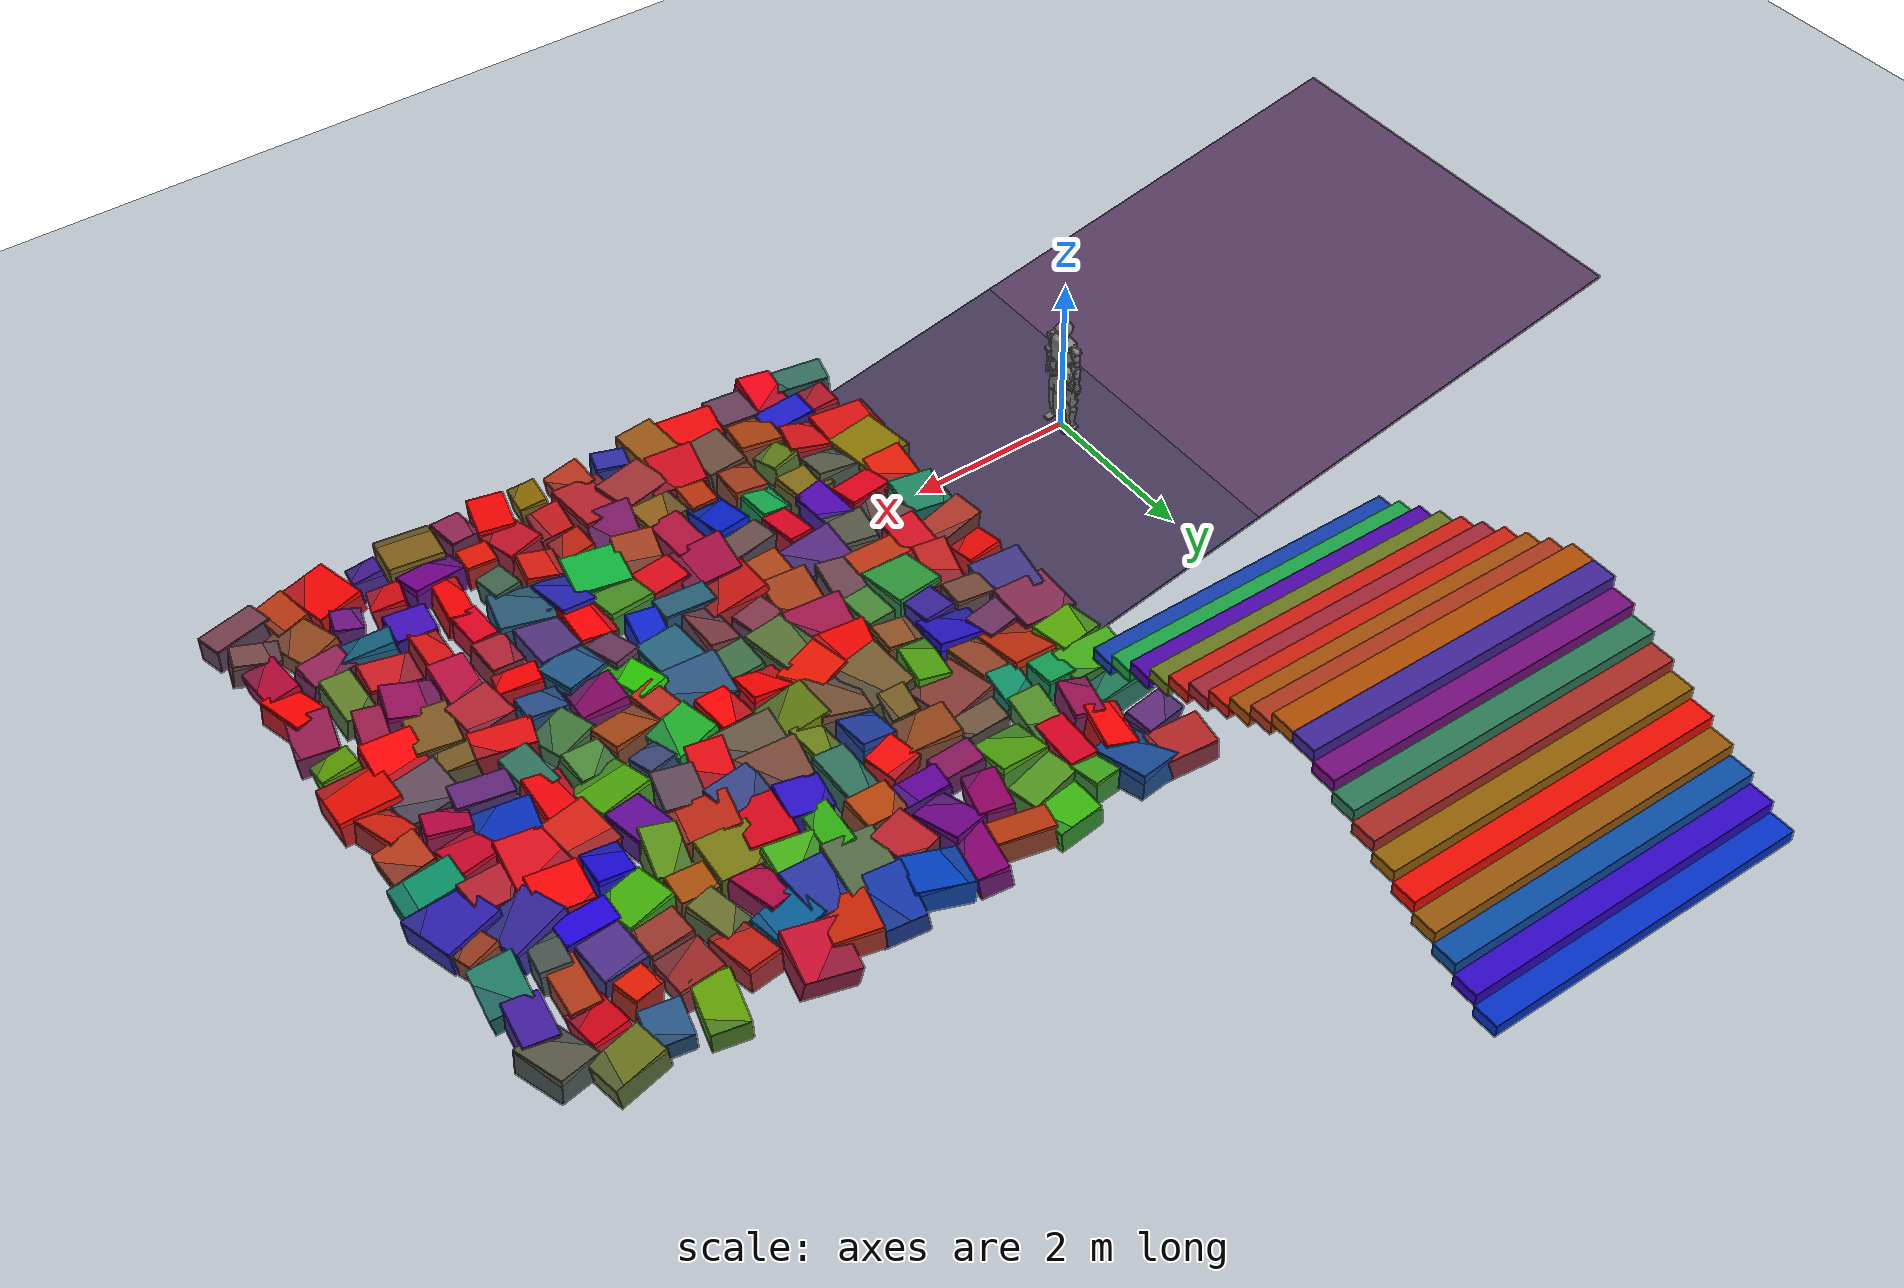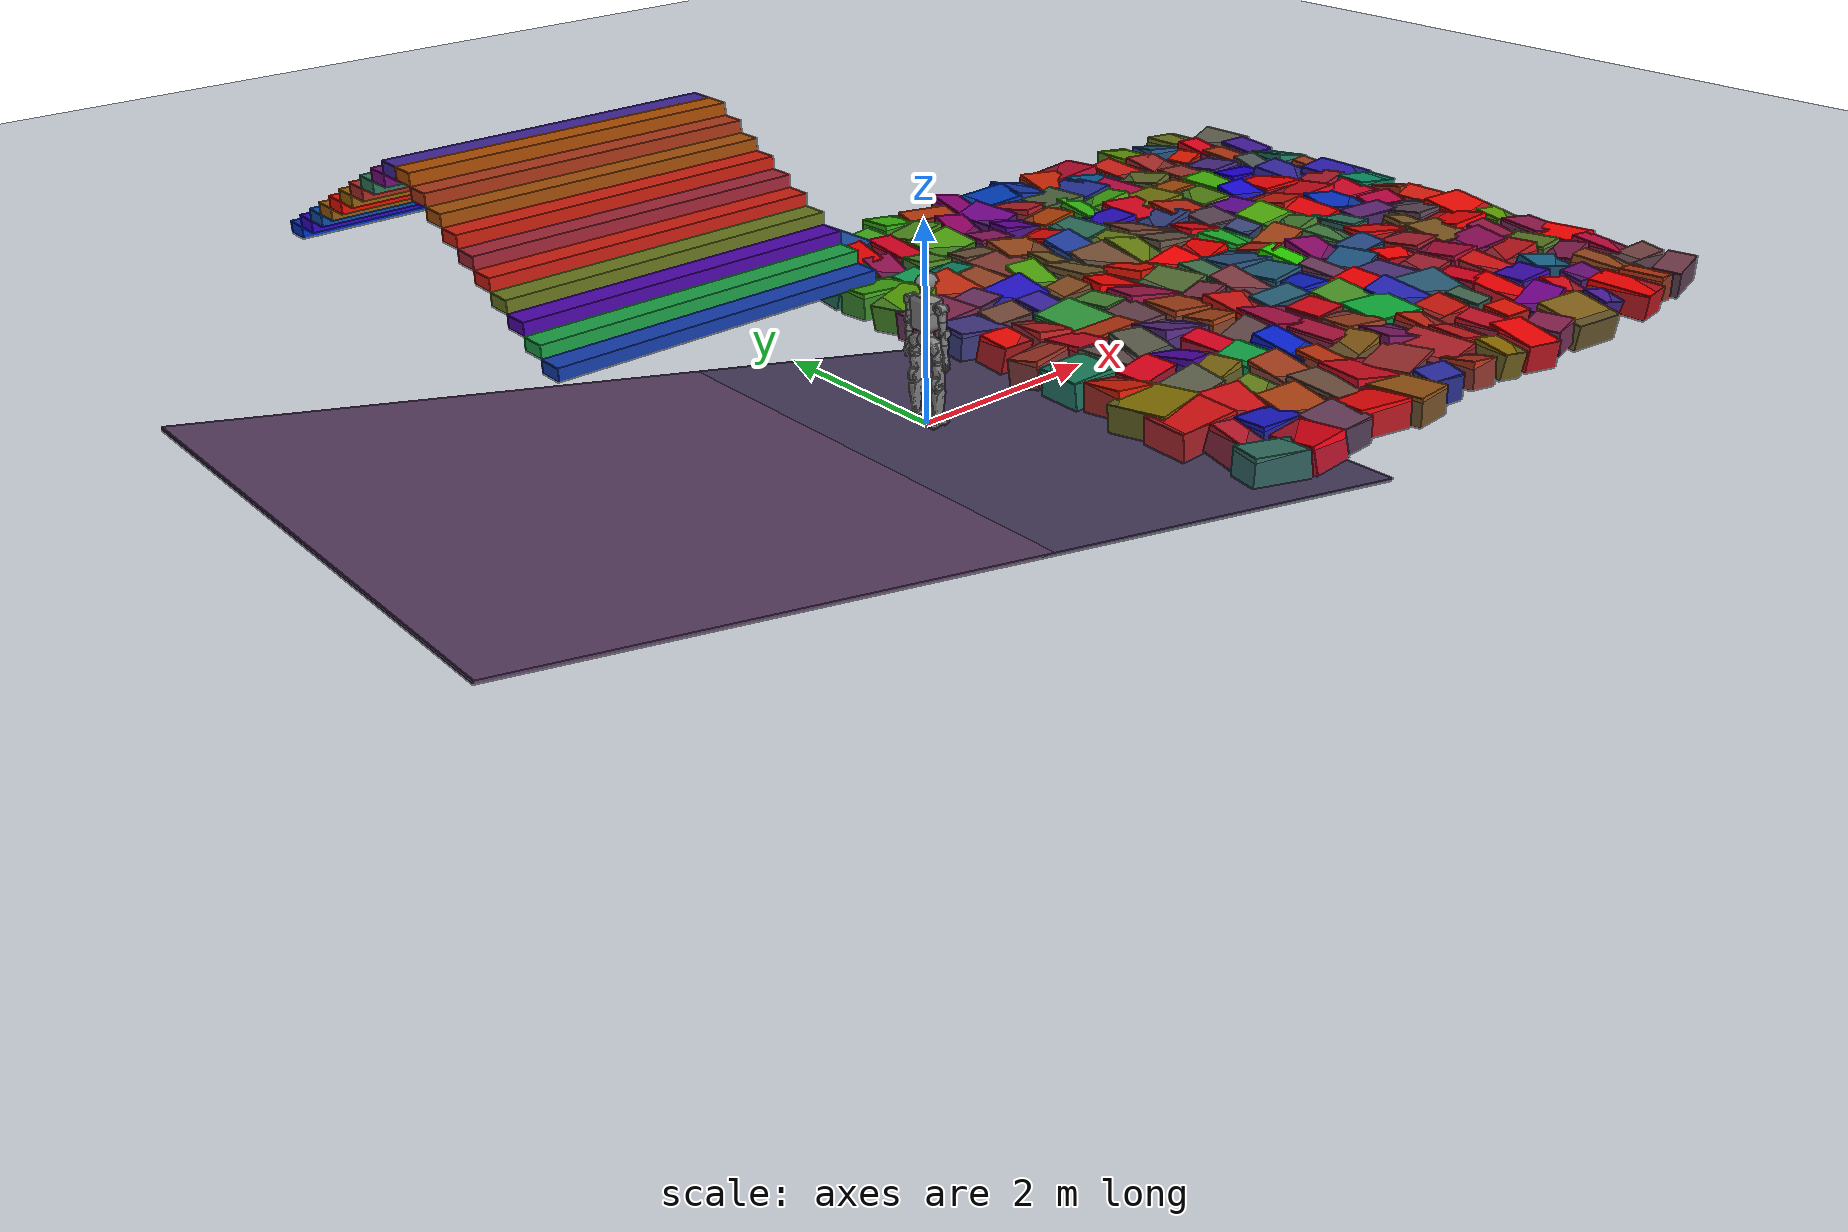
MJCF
<mujoco model="sr02h_v1">
  <compiler angle="radian" meshdir="../meshes/" />
  <statistic meansize="0.201559" extent="2.948112" center="0.00499457 0 0.337764" />

  <default>
    <joint limited="true" damping="0.01" armature="0.01" frictionloss="0.01" />
    <equality solref="0.001 2" />
    <default class="visual">
      <geom type="mesh" contype="0" conaffinity="0" group="2" density="0" />
    </default>
    <default class="collision">
        <geom group="1" priority="1" rgba="0.89804 0.91765 0.92941 0" friction="1. 1.0 1.0" density="0" />
    </default>

    <geom condim="4" contype="1" conaffinity="15" solref="0.001 2" friction="0.9 0.2 0.2" />
  </default>

  <asset>

    <texture name="grid" type="2d" builtin="checker" width="512" height="512" rgb1=".1 .2 .3" rgb2=".2 .3 .4" />
    <material name="grid" texture="grid" texrepeat="1 1" texuniform="true" reflectance=".2" />
  </asset>

  <option timestep="0.001" integrator="RK4">
    <flag frictionloss="enable" />
  </option>

  <asset>
    <material name="metal" rgba=".9 .95 .95 1" />
    <material name="black" rgba="0 0 0 1" />
    <material name="white" rgba="1 1 1 1" />
    <material name="gray" rgba="0.4 0.4 0.4 1" />
    <material name="transparent" rgba="0.5 0.5 0.5 1" />
    <mesh name="base_link" file="base_link.STL" />
    <mesh name="left_hip_pitch" file="left_hip_pitch.STL" />
    <mesh name="left_hip_roll" file="left_hip_roll.STL" />
    <mesh name="left_hip_yaw" file="left_hip_yaw.STL" />
    <mesh name="left_knee" file="left_knee.STL" />
    <mesh name="left_ankle_pitch" file="left_ankle_pitch.STL" />
    <mesh name="left_ankle_roll" file="left_ankle_roll.STL" />
    <mesh name="right_hip_pitch" file="right_hip_pitch.STL" />
    <mesh name="right_hip_roll" file="right_hip_roll.STL" />
    <mesh name="right_hip_yaw" file="right_hip_yaw.STL" />
    <mesh name="right_knee" file="right_knee.STL" />
    <mesh name="right_ankle_pitch" file="right_ankle_pitch.STL" />
    <mesh name="right_ankle_roll" file="right_ankle_roll.STL" />
    <mesh name="upper_body" file="upper_body.STL" />
    <mesh name="left_shoulder_pitch" file="left_shoulder_pitch.STL" />
    <mesh name="left_shoulder_roll" file="left_shoulder_roll.STL" />
    <mesh name="left_shoulder_yaw" file="left_shoulder_yaw.STL" />
    <mesh name="left_elbow_pitch" file="left_elbow_pitch.STL" />
    <mesh name="left_elbow_yaw" file="left_elbow_yaw.STL" />
    <mesh name="right_shoulder_pitch" file="right_shoulder_pitch.STL" />
    <mesh name="right_shoulder_roll" file="right_shoulder_roll.STL" />
    <mesh name="right_shoulder_yaw" file="right_shoulder_yaw.STL" />
    <mesh name="right_elbow_pitch" file="right_elbow_pitch.STL" />
    <mesh name="right_elbow_yaw" file="right_elbow_yaw.STL" />
    <mesh name="head" file="head.STL" />
  </asset>

  <worldbody>
    <light name="main_light" diffuse="2 2 2" specular="0.5 0.5 0.5" pos="0 0 40" dir="0 0 -1" castshadow="true" />

    <light name="aux_light1" diffuse=".8 .8 .8" pos=" 10 0 1" dir="-1 0 0" castshadow="false" />
    <light name="aux_light2" diffuse=".8 .8 .8" pos="-10 0 1" dir=" 1 0 0" castshadow="false" />
    <light name="aux_light3" diffuse=".8 .8 .8" pos="0  10 1" dir="0 -1 0" castshadow="false" />
    <light name="aux_light4" diffuse=".8 .8 .8" pos="0 -10 1" dir="0  1 0" castshadow="false" />
    <geom name="floor" type="plane" size="0 0 0.05" material="grid" />

    <body name="base_link" pos="0 0 0.78">
      <freejoint />
      <inertial pos="-0.00016099 4.8814e-06 0.086352" quat="0.503386 0.496667 0.495428 0.504456" mass="3.47645" diaginertia="0.0062779 0.00569814 0.00551335" />
      <geom type="mesh" class="visual" mesh="base_link" />
      <site name="imu_site" pos="0 0 0" size="0.02" rgba="1 0 0 1" type="sphere" />
      <site name="imu" size="0.01" pos="0.0 0 0.0" />

      <body name="left_hip_pitch_link" pos="0 0.058 0.064402">
        <inertial pos="0.00279811 0.0590227 -0.0230549" quat="0.635667 0.294909 -0.25916 0.664675" mass="0.765649" diaginertia="0.00273954 0.00226518 0.00179678" />
        <joint name="left_hip_pitch_joint" pos="0 0 0" axis="0 1 0" range="-1.57 1.57" actuatorfrcrange="-200 200" />
        <geom type="mesh" class="visual" mesh="left_hip_pitch" />
        <body name="left_hip_roll_link" pos="0.02925 0.083 -0.045">
          <inertial pos="-0.0287468 0.00686267 -0.0500657" quat="0.998029 0.0627218 0.00169713 0.000589256" mass="2.1935" diaginertia="0.00872027 0.0081648 0.00302264" />
          <joint name="left_hip_roll_joint" pos="0 0 0" axis="1 0 0" range="-0.5 1.48" actuatorfrcrange="-200 200" />
          <geom type="mesh" class="visual" mesh="left_hip_roll" />
          <body name="left_hip_yaw_link" pos="-0.02925 0.012546 -0.132">
            <inertial pos="0.000859034 0.0027923 -0.123047" quat="0.999791 -0.00555855 0.0188583 -0.00555928" mass="0.997693" diaginertia="0.00858731 0.00821025 0.00230384" />
            <joint name="left_hip_yaw_joint" pos="0 0 0" axis="0 0 1" range="-2.56 2.56" actuatorfrcrange="-200 200" />
            <geom type="mesh" class="visual" mesh="left_hip_yaw" />
            <body name="left_knee_link" pos="-0.010001 0 -0.2165">
              <inertial pos="0.00380647 0.00059334 -0.0787131" quat="0.704094 -0.0019289 -0.00205998 0.710101" mass="3.18942" diaginertia="0.0344715 0.0333337 0.00411457" />
              <joint name="left_knee_joint" pos="0 0 0" axis="0 1 0" range="-0.2 2.55" actuatorfrcrange="-200 200" />
              <geom type="mesh" class="visual" mesh="left_knee" />
              <body name="left_ankle_pitch_link" pos="0 0 -0.35">
                <inertial pos="0.00113045 0 -0.00399755" quat="0.500022 0.499956 -0.500017 0.500004" mass="0.2" diaginertia="4.3137e-05 2.9623e-05 2.6222e-05" />
                <joint name="left_ankle_pitch_joint" pos="0 0 0" axis="0 1 0" range="-0.92 0.61" actuatorfrcrange="-200 200" />
                <geom type="mesh" class="visual" mesh="left_ankle_pitch" />
                <body name="left_ankle_roll_link" pos="0 0 -0.016">
                  <inertial pos="0.006 -2.45147e-05 -0.0216902" quat="0.707793 0.00726632 0.706347 -0.00707932" mass="0.528202" diaginertia="0.00271856 0.0024795 0.00038654" />
                  <joint name="left_ankle_roll_joint" pos="0 0 0" axis="1 0 0" range="-0.8 0.8" actuatorfrcrange="-200 200" />
                  <geom type="mesh" class="visual" mesh="left_ankle_roll" />
                  <geom type="mesh" class="collision" mesh="left_ankle_roll" />
                </body>
              </body>
            </body>
          </body>
        </body>
      </body>
      <body name="right_hip_pitch_link" pos="0 -0.058 0.064402">
        <inertial pos="0.00275303 -0.0589431 -0.0230019" quat="0.295135 0.635489 -0.66474 0.259172" mass="0.765633" diaginertia="0.0027395 0.0022653 0.00179669" />
        <joint name="right_hip_pitch_joint" pos="0 0 0" axis="0 1 0" range="-1.57 1.57" actuatorfrcrange="-200 200" />
        <geom type="mesh" class="visual" mesh="right_hip_pitch" />
        <body name="right_hip_roll_link" pos="0.02925 -0.083 -0.045">
          <inertial pos="-0.0287405 -0.00684507 -0.0500719" quat="0.998043 -0.0625016 0.00171536 -0.000407591" mass="2.19349" diaginertia="0.00871957 0.00816402 0.00302271" />
          <joint name="right_hip_roll_joint" pos="0 0 0" axis="1 0 0" range="-1.48 0.5" actuatorfrcrange="-200 200" />
          <geom type="mesh" class="visual" mesh="right_hip_roll" />
          <body name="right_hip_yaw_link" pos="-0.02925 -0.012498 -0.132">
            <inertial pos="0.000860684 -0.00280479 -0.123053" quat="0.999773 0.00558237 0.0198002 0.00545366" mass="0.978452" diaginertia="0.00853411 0.00815256 0.00225813" />
            <joint name="right_hip_yaw_joint" pos="0 0 0" axis="0 0 1" range="-2.56 2.56" actuatorfrcrange="-200 200" />
            <geom type="mesh" class="visual" mesh="right_hip_yaw" />
            <body name="right_knee_link" pos="-0.010001 0 -0.2165">
              <inertial pos="0.00380647 -0.00059334 -0.0787131" quat="0.702284 0.000581247 -0.000340368 0.711896" mass="3.22332" diaginertia="0.0356009 0.0344374 0.00416784" />
              <joint name="right_knee_joint" pos="0 0 0" axis="0 1 0" range="-0.2 2.55" actuatorfrcrange="-200 200" />
              <geom type="mesh" class="visual" mesh="right_knee" />
              <body name="right_ankle_pitch_link" pos="0 0 -0.35">
                <inertial pos="0.00111916 0 -0.00395618" quat="0.500017 0.500004 -0.500022 0.499956" mass="0.2" diaginertia="4.3137e-05 2.9623e-05 2.6222e-05" />
                <joint name="right_ankle_pitch_joint" pos="0 0 0" axis="0 1 0" range="-0.92 0.61" actuatorfrcrange="-200 200" />
                <geom type="mesh" class="visual" mesh="right_ankle_pitch" />
                <body name="right_ankle_roll_link" pos="0 0 -0.015999">
                  <inertial pos="0.006 -2.45147e-05 -0.0216902" quat="0.707793 0.00726632 0.706347 -0.00707932" mass="0.528202" diaginertia="0.00271856 0.0024795 0.00038654" />
                  <joint name="right_ankle_roll_joint" pos="0 0 0" axis="1 0 0" range="-0.8 0.8" actuatorfrcrange="-200 200" />
                  <geom type="mesh" class="visual" mesh="right_ankle_roll" />
                  <geom type="mesh" class="collision" mesh="right_ankle_roll" />
                </body>
              </body>
            </body>
          </body>
        </body>
      </body>
      <body name="waist_link" pos="0 0 0.1699">
        <inertial pos="0.0050879 4.5814e-05 0.16257" quat="0.999967 -0.00176402 -0.00792572 -0.000570994" mass="18.4507" diaginertia="0.167495 0.139809 0.108815" />
        <joint name="waist_joint" pos="0 0 0" axis="0 0 1" range="-2.13 2.13" actuatorfrcrange="-200 200" />
        <geom type="mesh" class="visual" mesh="upper_body" />
        <geom size="0.2 0.175 0.3" pos="0 0 0.2" type="box" class="collision" />

        <camera name="depth_camera" pos="0.12380269 -0.0475 0.22030226" euler="0 -0.6981320 -1.5707963" mode="fixed" fovy="60" />
        <body name="left_shoulder_pitch_link" pos="0 0.1665 0.2571">
          <inertial pos="0.00344718 0.0423351 -0.00711074" quat="0.843856 0.0101112 0.0292772 0.535674" mass="0.694216" diaginertia="0.000615881 0.000567583 0.000517536" />
          <joint name="left_shoulder_pitch_joint" pos="0 0 0" axis="0 1 0" range="-3.14 0.79" actuatorfrcrange="-200 200" />
          <geom type="mesh" class="visual" mesh="left_shoulder_pitch" />
          <body name="left_shoulder_roll_link" pos="0.04075 0.046 -0.008">
            <inertial pos="-0.0432706 0.00701098 -0.0598413" quat="0.71124 8.00439e-05 0.000546331 0.702949" mass="0.746183" diaginertia="0.00112597 0.00112597 0.00112597" />
            <joint name="left_shoulder_roll_joint" pos="0 0 0" axis="1 0 0" range="-0.19 1.9" actuatorfrcrange="-200 200" />
            <geom type="mesh" class="visual" mesh="left_shoulder_roll" />
            <body name="left_shoulder_yaw_link" pos="-0.043 0.011038 -0.10895" quat="0.999048 0.0436192 0 0">
              <inertial pos="0.0112065 -0.000982862 -0.0977927" quat="0.598219 0.0452388 -0.0651491 0.797397" mass="0.703549" diaginertia="0.00157655 0.00152585 0.000507596" />
              <joint name="left_shoulder_yaw_joint" pos="0 0 0" axis="0 0 1" range="-2.27 2.27" actuatorfrcrange="-200 200" />
              <geom type="mesh" class="visual" mesh="left_shoulder_yaw" />
              <body name="left_elbow_pitch_link" pos="0.015164 -0.034428 -0.119">
                <inertial pos="-0.00854578 0.0363085 -0.0544777" quat="0.5 0.5 -0.5 0.5" mass="0.637811" diaginertia="0.0008168 0.0005975 0.0005157" />
                <joint name="left_elbow_pitch_joint" pos="0 0 0" axis="0 1 0" range="-2.32 0.52" actuatorfrcrange="-200 200" />
                <geom type="mesh" class="visual" mesh="left_elbow_pitch" />
                <body name="left_elbow_yaw_link" pos="-0.010169 0.035352 -0.1">
                  <inertial pos="0.000193821 0.00135316 -0.100679" quat="0.707107 0 0 0.707107" mass="0.354681" diaginertia="0.0011323 0.0011202 0.0003334" />
                  <joint name="left_elbow_yaw_joint" pos="0 0 0" axis="0 0 1" range="-2.62 2.62" actuatorfrcrange="-200 200" />
                  <geom type="mesh" class="visual" mesh="left_elbow_yaw" />
                </body>
              </body>
            </body>
          </body>
        </body>
        <body name="right_shoulder_pitch_link" pos="0 -0.1665 0.2571">
          <inertial pos="0.00354004 -0.041889 -0.01071" quat="0.536947 0.0214037 0.0390001 0.842442" mass="0.681333" diaginertia="0.000615738 0.000567862 0.0005174" />
          <joint name="right_shoulder_pitch_joint" pos="0 0 0" axis="0 1 0" range="-3.14 0.79" actuatorfrcrange="-200 200" />
          <geom type="mesh" class="visual" mesh="right_shoulder_pitch" />
          <body name="right_shoulder_roll_link" pos="0.04075 -0.046 -0.008">
            <inertial pos="-0.043081 -0.00701174 -0.0597939" quat="0.71124 8.00439e-05 0.000546331 0.702949" mass="0.740047" diaginertia="0.00112597 0.00112597 0.00112597" />
            <joint name="right_shoulder_roll_joint" pos="0 0 0" axis="1 0 0" range="-1.9 0.19" actuatorfrcrange="-200 200" />
            <geom type="mesh" class="visual" mesh="right_shoulder_roll" />
            <body name="right_shoulder_yaw_link" pos="-0.043 -0.011038 -0.10895" quat="0.999048 -0.0436192 0 0">
              <inertial pos="0.011211 -0.00749887 -0.0980614" quat="0.797397 -0.0651491 0.0452388 0.598219" mass="0.697149" diaginertia="0.00157655 0.00152585 0.000507596" />
              <joint name="right_shoulder_yaw_joint" pos="0 0 0" axis="0 0 1" range="-2.27 2.27" actuatorfrcrange="-200 200" />
              <geom type="mesh" class="visual" mesh="right_shoulder_yaw" />
              <body name="right_elbow_pitch_link" pos="0.015164 0.034428 -0.119">
                <inertial pos="-0.00831411 -0.0409275 -0.0509462" quat="0.5 0.5 -0.5 0.5" mass="0.630886" diaginertia="0.0008168 0.0005975 0.0005157" />
                <joint name="right_elbow_pitch_joint" pos="0 0 0" axis="0 1 0" range="-2.32 0.52" actuatorfrcrange="-200 200" />
                <geom type="mesh" class="visual" mesh="right_elbow_pitch" />
                <body name="right_elbow_yaw_link" pos="-0.010169 -0.035352 -0.1">
                  <inertial pos="0.000193054 -0.0100877 -0.102025" quat="0.707107 0 0 0.707107" mass="0.345282" diaginertia="0.0011323 0.0011202 0.0003334" />
                  <joint name="right_elbow_yaw_joint" pos="0 0 0" axis="0 0 1" range="-2.62 2.62" actuatorfrcrange="-200 200" />
                  <geom type="mesh" class="visual" mesh="right_elbow_yaw" />
                </body>
              </body>
            </body>
          </body>
        </body>
        <body name="head_link" pos="0 0 0.3401">
          <inertial pos="0.010687 -0.00052293 0.081441" quat="0.713122 0.167422 0.165155 0.660417" mass="0.9238" diaginertia="0.00486206 0.00455249 0.00376545" />
          <joint name="head_joint" pos="0 0 0" axis="0 0 1" range="-1.5 1.5" actuatorfrcrange="-200 200" />
          <geom type="mesh" class="visual" mesh="head" />
        </body>
      </body>
    </body>
  <geom pos="1.957998042133926 -2.4992930254108257 -0.145" type="box" size="0.33284301412691336 0.17190332828962948 0.14583456783283522" quat="0.9909703522191986 -0.016090884434349292 0.042958084200668746 -0.1259898704757095" rgba="0.19797179168330903 0.43408488871196726 0.3679433196047237 1.0" /><geom pos="1.957998042133926 -2.04164810312137 -0.145" type="box" size="0.15504156573101513 0.21296277402406677 0.14711378646530307" quat="0.993819590722818 0.07778540765322897 0.059123237014948295 -0.052692450091314964" rgba="0.7410670045996289 0.09328382169963209 0.16564917370073898 1.0" /><geom pos="1.957998042133926 -1.5032617985927885 -0.145" type="box" size="0.3480961174820182 0.26322401329441203 0.14693738688123495" quat="0.9988785892388499 -0.0024964731176919837 -0.03478489060503115 -0.03202097699592599" rgba="0.8627970793467399 0.07071057307508904 0.06649234757817107 1.0" /><geom pos="1.957998042133926 -1.0520911381626208 -0.145" type="box" size="0.3221830152833198 0.32323581275554625 0.14895729064125438" quat="0.9955381046640194 -0.03239659982857167 -0.018413573957020455 0.08669073062126513" rgba="0.5281927192219263 0.4585184994469527 0.013288781331120936 1.0" /><geom pos="1.957998042133926 -0.5824820812563996 -0.145" type="box" size="0.22998985453253795 0.25438637066299075 0.14792810590702044" quat="0.9947820976324406 -0.0761288336392577 0.055186910393227734 -0.0395901987867886" rgba="0.8738967943791037 0.10908943637598542 0.017013769244910854 1.0" /><geom pos="1.957998042133926 -0.04435744324730306 -0.145" type="box" size="0.26710529215627515 0.2743300351984773 0.14958595057253682" quat="0.997378088943967 -0.026908897191115225 -0.0353852958272554 -0.057102887717312326" rgba="0.11148267762315811 0.5175938472176064 0.3709234751592355 1.0" /><geom pos="1.957998042133926 0.4948537146982699 -0.145" type="box" size="0.32566342237588164 0.17686736630899058 0.14836432819535736" quat="0.9902690481598455 -0.08548940784661545 0.01340621714837004 0.10899103974364024" rgba="0.6507214301908031 0.20202426935695578 0.14725430045224114 1.0" /><geom pos="1.957998042133926 1.0348074709707262 -0.145" type="box" size="0.21252736029380134 0.1780899640800102 0.1494637187049017" quat="0.9955655171606638 0.070787776227392 0.04531384643723586 0.042249817732900645" rgba="0.949787120516316 0.036326895964582745 0.01388598351910128 1.0" /><geom pos="1.957998042133926 1.5811788969334764 -0.145" type="box" size="0.29907242219580465 0.31097916849848667 0.14736373859750082" quat="0.9957579633755859 -0.012655916699348702 0.04562210006915291 -0.07889569146591377" rgba="0.2591927875449006 0.21233032935752075 0.5284768830975787 1.0" /><geom pos="1.957998042133926 2.0530902520637904 -0.145" type="box" size="0.32459481451954164 0.3070829613531464 0.15107888355893875" quat="0.9991952791219699 -0.02703193432072591 -0.02942036211576596 -0.0035370892307044132" rgba="0.5213064935681245 0.16801163268688687 0.31068187374498857 1.0" /><geom pos="1.957998042133926 2.6022648669621553 -0.145" type="box" size="0.29627225296251497 0.22157621791761548 0.15380921135084175" quat="0.9909041541545917 -0.02436102544436694 -0.07496025455603089 0.10907088500313541" rgba="0.3345677187653432 0.646368119842533 0.019064161392123857 1.0" /><geom pos="1.957998042133926 3.058627676870308 -0.145" type="box" size="0.3472007632139931 0.2159430651719212 0.14908365893757275" quat="0.9979295627135039 -0.047691851650669304 0.028753870329402863 -0.032175924068241796" rgba="0.25331191047940593 0.6599013368084162 0.08678675271217784 1.0" /><geom pos="1.957998042133926 3.531264936929265 -0.145" type="box" size="0.33448742479818655 0.163314408115717 0.15087970752599072" quat="0.995989133423796 0.0730795215944524 0.04321847965693501 0.028234600074819968" rgba="0.1363865095697575 0.5061445770271663 0.3574689134030762 1.0" /><geom pos="1.957998042133926 4.079383163075269 -0.145" type="box" size="0.28810881893243384 0.16530304700679888 0.15168068987369032" quat="0.9879295692189897 -0.07656667245480465 -0.0829341680952444 0.1060878630868292" rgba="0.3635783580142745 0.16377994614253982 0.47264169584318566 1.0" /><geom pos="1.957998042133926 4.557279350375866 -0.145" type="box" size="0.3138954689396323 0.22594448634441894 0.14716775980072244" quat="0.9964428749348843 -0.002065490280921509 0.04290334591481735 -0.07250264581872594" rgba="0.7061916166603961 0.14456387563390233 0.14924450770570158 1.0" /><geom pos="2.444516059464894 -2.523621146134275 -0.145" type="box" size="0.21186196804782606 0.2807804314820017 0.14705348057073023" quat="0.9938244709388897 -0.08415418104040531 -0.058861987547304644 -0.04202691040792221" rgba="0.9178498603602471 0.0002615449616682486 0.08188859467808468 1.0" /><geom pos="2.444516059464894 -2.040341564825053 -0.145" type="box" size="0.2907109467133618 0.17733883619988783 0.14679862560357843" quat="0.9989507241952216 -0.02038582098058318 0.04101056951818507 4.604980168222358e-05" rgba="0.11355771215690391 0.10178211821328999 0.7846601696298061 1.0" /><geom pos="2.444516059464894 -1.5429889233940004 -0.145" type="box" size="0.28600473754657146 0.2521632625445939 0.1516159815753087" quat="0.9864218251085122 0.055734066950462555 -0.0533564284905039 -0.14497857865729954" rgba="0.841136530793276 0.06929602906059752 0.08956744014612648 1.0" /><geom pos="2.444516059464894 -1.020509579576122 -0.145" type="box" size="0.3280813445051767 0.20692717465217741 0.1496262017311557" quat="0.994377487832843 0.07176521922454845 -0.07727342348900901 -0.009590778028142738" rgba="0.3508804714835555 0.3656230486745657 0.2834964798418788 1.0" /><geom pos="2.444516059464894 -0.48894151689398235 -0.145" type="box" size="0.26850382703063325 0.1788977245233625 0.14739367197281827" quat="0.9964241767116899 0.03497787888444795 -0.018664850984936393 0.07461254178009165" rgba="0.8931687743556569 0.0031074890552385552 0.10372373658910455 1.0" /><geom pos="2.444516059464894 0.015776377405987585 -0.145" type="box" size="0.18467216083585192 0.28112284625187367 0.15169433602919405" quat="0.9866153932239887 0.03817902063057468 0.06196316964555538 0.1459211905263949" rgba="0.3941029495496374 0.312668915087742 0.29322813536262055 1.0" /><geom pos="2.444516059464894 0.526709978746664 -0.145" type="box" size="0.19849893184672407 0.32862384006711665 0.15241528756794634" quat="0.9979703500229016 -0.06241956439388969 0.010100019384288157 -0.007547719157546136" rgba="0.8154828095327682 0.050789181392460706 0.13372800907477111 1.0" /><geom pos="2.444516059464894 0.9890716314220693 -0.145" type="box" size="0.18946930922307673 0.29722638333942686 0.1462315823510527" quat="0.9878429137278376 -0.08183315032985883 0.048112012733118784 -0.1231054325996831" rgba="0.748695917678422 0.12692643746890625 0.12437764485267172 1.0" /><geom pos="2.444516059464894 1.5314362800494399 -0.145" type="box" size="0.22770995901149033 0.18171930943992676 0.15402598616643912" quat="0.9975490299952499 0.038513557105042694 -0.03198130595979493 -0.048885936052803704" rgba="0.4742382882080046 0.29090982677343985 0.23485188501855553 1.0" /><geom pos="2.444516059464894 2.0355356049802644 -0.145" type="box" size="0.2687015179103335 0.1905099341310616 0.1513873248215232" quat="0.9952425063288406 0.01360052863354081 -0.011211603466958315 0.09582107891730167" rgba="0.4277407417149037 0.19187329814813914 0.38038596013695714 1.0" /><geom pos="2.444516059464894 2.4918759859365087 -0.145" type="box" size="0.3312854066602587 0.3179370147265603 0.14785717400398388" quat="0.9952405889456838 0.0791163815214464 -0.051509214198560034 0.024157175800334604" rgba="0.7726471497661098 0.17182205494197603 0.05553079529191415 1.0" /><geom pos="2.444516059464894 2.9550064010883146 -0.145" type="box" size="0.17168483791147782 0.2295138161286475 0.1529558017561928" quat="0.9986250531959017 0.025704034270107524 -0.042186515796522765 0.017538632691107187" rgba="0.06954520315776502 0.6189401405978279 0.3115146562444071 1.0" /><geom pos="2.444516059464894 3.502042609151612 -0.145" type="box" size="0.16566162778598847 0.2801226131500454 0.14555705052870826" quat="0.9879574654410053 0.042356266250829715 -0.040603249693457355 -0.1431690235456135" rgba="0.5995748988430568 0.07063935719221297 0.3297857439647302 1.0" /><geom pos="2.444516059464894 3.9788953857596594 -0.145" type="box" size="0.18206852376076016 0.31037810586694287 0.15338440507105508" quat="0.9869374475514968 -0.001052220007180275 -0.09246310060145287 -0.13192400267107826" rgba="0.9755318539908082 0.01333656052185332 0.011131585487338462 1.0" /><geom pos="2.444516059464894 4.44417074525991 -0.145" type="box" size="0.3166842092089295 0.3352686308964228 0.14946911273931965" quat="0.9887718071263224 0.055782475003722784 -0.08261560268519824 0.1113251593646621" rgba="0.0966783060147347 0.2962575971756643 0.607064096809601 1.0" /><geom pos="2.916342342515368 -2.4559510775218723 -0.145" type="box" size="0.24392645659414955 0.2480396523250809 0.15012502294176475" quat="0.9992475228551296 0.010839888263251649 -0.030558812365102078 -0.021284827393285292" rgba="0.40992169886458074 0.23907390543035129 0.351004395705068 1.0" /><geom pos="2.916342342515368 -1.9803028987844153 -0.145" type="box" size="0.25252682102152985 0.28864561786538545 0.14789457906298856" quat="0.9947289749067135 0.05607279889957505 -0.02799988662161425 -0.08115487695624696" rgba="0.6800134561216474 0.2519257784251913 0.06806076545316125 1.0" /><geom pos="2.916342342515368 -1.4696403790650296 -0.145" type="box" size="0.18303096731172172 0.17434268609011233 0.1472178677900903" quat="0.9892470704767582 0.08135578763545631 0.03828283208817285 0.1153511774481523" rgba="0.39543045864328974 0.5109020324830037 0.09366750887370656 1.0" /><geom pos="2.916342342515368 -0.940775509448021 -0.145" type="box" size="0.257466963160319 0.20847923477249047 0.1535882910751828" quat="0.9933068865553027 -0.028520244087792763 -0.08410608717797519 0.07385249419345578" rgba="0.5053414281940739 0.41800826411862363 0.07665030768730247 1.0" /><geom pos="2.916342342515368 -0.46236018972493387 -0.145" type="box" size="0.1808254605174423 0.3283203746404676 0.14816995667561775" quat="0.9925919900927093 -0.08467289791606832 0.04877728042313054 0.07219708080534536" rgba="0.30514790006057124 0.021604604778549148 0.6732474951608796 1.0" /><geom pos="2.916342342515368 0.0026884108771549897 -0.145" type="box" size="0.22831958608355807 0.2890890251624114 0.15276175304030787" quat="0.9909342972352649 0.06162299388772869 0.006117748907411651 -0.11922415164500219" rgba="0.354996723883786 0.35579375011587305 0.28920952600034094 1.0" /><geom pos="2.916342342515368 0.5035277679885786 -0.145" type="box" size="0.3412946443319198 0.15877846618008945 0.15133138122866363" quat="0.9990976812148902 -0.04029069568985144 -0.004926992030244906 -0.01249831914264422" rgba="0.7256793597942196 0.20573864766749617 0.06858199253828423 1.0" /><geom pos="2.916342342515368 0.9550893346899247 -0.145" type="box" size="0.29171982746609537 0.32487330429185446 0.15460809025661312" quat="0.9972614825293 0.043266678889126976 -0.01614197542310325 0.057766483282327766" rgba="0.17716167523840232 0.5944385114324767 0.22839981332912096 1.0" /><geom pos="2.916342342515368 1.4556674853843852 -0.145" type="box" size="0.1907203239605426 0.2379807468603924 0.15244589122510335" quat="0.9974456120134895 0.06341492195129322 0.013051517414801508 0.030173774078131488" rgba="0.22860430636235274 0.14343560613028508 0.6279600875073622 1.0" /><geom pos="2.916342342515368 1.9151637447378027 -0.145" type="box" size="0.3168434043073396 0.2557800802616688 0.1529003027212154" quat="0.9932785837220449 0.08284626711030248 -0.07528564403803878 -0.029431665715602153" rgba="0.14724417665244838 0.07424695191823558 0.778508871429316 1.0" /><geom pos="2.916342342515368 2.4224037524963506 -0.145" type="box" size="0.23504022476812506 0.2883811747017142 0.1480508796905882" quat="0.9963444033420187 0.036063665005739466 -0.057594580176835955 0.051769743380132516" rgba="0.589153272959651 0.2655608395013529 0.14528588753899607 1.0" /><geom pos="2.916342342515368 2.917928152709364 -0.145" type="box" size="0.18237052261611736 0.23937067794021544 0.14671656564344596" quat="0.9950650482833898 -0.08105185923797859 -0.04641779506449478 -0.03348931322366182" rgba="0.060363908893961815 0.5438670409719215 0.3957690501341167 1.0" /><geom pos="2.916342342515368 3.433314861168924 -0.145" type="box" size="0.1860495720841253 0.33436929659136094 0.14510370007265735" quat="0.9959827113017278 -0.06680944399135787 0.03552165484630272 -0.04788683554594901" rgba="0.3113802376192276 0.5462317487004494 0.14238801368032294 1.0" /><geom pos="2.916342342515368 3.894644596559746 -0.145" type="box" size="0.1657260402876255 0.3342028655318849 0.15304901861949896" quat="0.998740708113171 0.029419796063516475 0.019884895324628758 -0.03544100019908489" rgba="0.8654721239698195 0.0022864839987679297 0.13224139203141252 1.0" /><geom pos="2.916342342515368 4.37216152277909 -0.145" type="box" size="0.18416098963565006 0.18955014039720242 0.14807502978407366" quat="0.996294096354811 0.04219582952780853 -0.03168189968695282 0.06792527343512582" rgba="0.2430950018312218 0.6481062644141407 0.10879873375463756 1.0" /><geom pos="3.454586286283903 -2.4507929705620395 -0.145" type="box" size="0.3254125479420703 0.2380292856902174 0.15208178539458364" quat="0.9948859250624749 -0.04975173100734678 0.025674933282381043 -0.08406877645892974" rgba="0.9350630230001009 0.028120119440422392 0.036816857559476696 1.0" /><geom pos="3.454586286283903 -1.9275705501933686 -0.145" type="box" size="0.23430091230416886 0.31823527037065624 0.15250996009942616" quat="0.9985473866288158 0.02483705112458014 0.04715498891568085 -0.00791483218769944" rgba="0.43781387242102277 0.31251314869441305 0.2496729788845642 1.0" /><geom pos="3.454586286283903 -1.4280451139055264 -0.145" type="box" size="0.2032511588962025 0.3288364553158126 0.1492237218084017" quat="0.9958466680121001 0.06756191759015943 -0.03995010984249089 -0.04613881039116093" rgba="0.6476330379168691 0.24127684246385073 0.11109011961928017 1.0" /><geom pos="3.454586286283903 -0.9077950932390184 -0.145" type="box" size="0.18518415127317944 0.21168605704957721 0.15076484519294522" quat="0.9951740242857101 0.01641238573030337 -0.0939306063423977 0.02315893291527458" rgba="0.06821102190846084 0.652214209640771 0.2795747684507681 1.0" /><geom pos="3.454586286283903 -0.4474635830438549 -0.145" type="box" size="0.15562900883002348 0.2542525003475209 0.15324299904541752" quat="0.9976252138684366 0.032382896485262866 -0.028724793713832953 0.053573938582846516" rgba="0.8748365436246752 0.0021769850665227233 0.12298647130880205 1.0" /><geom pos="3.454586286283903 0.08768866173553214 -0.145" type="box" size="0.345423770819894 0.24613160660670497 0.1480328470567551" quat="0.9930641909464711 -0.0765396275771608 0.08881656682763558 -0.00876444676704308" rgba="0.33927998833837103 0.15749374770911828 0.5032262639525107 1.0" /><geom pos="3.454586286283903 0.6362866276197758 -0.145" type="box" size="0.19898582474504128 0.33278152214585804 0.15299649881162267" quat="0.9951253629793076 -0.024301929474821977 -0.03869432686744588 -0.08739380554351293" rgba="0.42299498651664436 0.26841525153301077 0.3085897619503449 1.0" /><geom pos="3.454586286283903 1.1058572835418614 -0.145" type="box" size="0.1739706910160762 0.23015910293142233 0.15221407917649427" quat="0.9982858990268415 -0.032919224368528725 -0.016367783996596382 0.045537721925742444" rgba="0.27547296169699187 0.5239952181977938 0.2005318201052143 1.0" /><geom pos="3.454586286283903 1.621603702320682 -0.145" type="box" size="0.21966363860782445 0.18696591872096835 0.15142056010783303" quat="0.9961335815884639 -0.01213079404156497 -0.08305140393933222 -0.025946016483582746" rgba="0.5507958562070725 0.3119429183626805 0.137261225430247 1.0" /><geom pos="3.454586286283903 2.117255598446179 -0.145" type="box" size="0.18545099227356618 0.3488135292162005 0.15378197227795556" quat="0.9897864197436731 0.07296145531987994 -0.040208394449590186 -0.1156838551587582" rgba="0.304451277624044 0.6472500844290825 0.0482986379468735 1.0" /><geom pos="3.454586286283903 2.6396400923883423 -0.145" type="box" size="0.31633677414109335 0.30827679796106244 0.15002293225639543" quat="0.9943781670622648 0.02495792472556662 0.029941770033194846 0.09845127358527557" rgba="0.5436623011408571 0.24460672733743785 0.21173097152170503 1.0" /><geom pos="3.454586286283903 3.123495146682103 -0.145" type="box" size="0.26521994514322034 0.15546510255874899 0.1491692714874524" quat="0.9984710028019815 -0.03843703695949481 0.03854843040806067 -0.009605689275354455" rgba="0.43071526213658096 0.3320149967730527 0.23726974109036636 1.0" /><geom pos="3.454586286283903 3.64985137868059 -0.145" type="box" size="0.29472208877831313 0.24913987352548894 0.14901582575125938" quat="0.9962828449619626 0.06760525504122583 -0.04615274217476753 0.02683182280536183" rgba="0.31168570115212346 0.6337896725600223 0.05452462628785426 1.0" /><geom pos="3.454586286283903 4.172101784988177 -0.145" type="box" size="0.33414156096425507 0.1809949714222333 0.1539204202675898" quat="0.9903201669559433 -0.044499092112234497 -0.01453555974393945 0.13066948849854057" rgba="0.31257991487979764 0.5733865637812924 0.11403352133890998 1.0" /><geom pos="3.454586286283903 4.626997175289313 -0.145" type="box" size="0.2634369197155683 0.20581936704533593 0.15281517243724044" quat="0.9971700222068961 -0.024943679884877903 0.06790043615471288 0.020476582129317" rgba="0.2212897507481455 0.7218289788739594 0.05688127037789514 1.0" /><geom pos="3.9788978775770416 -2.500261476981687 -0.145" type="box" size="0.23682323977027295 0.3153064186549589 0.1545968951794319" quat="0.9987678573967668 -0.025837655228346343 0.011023242244444138 0.04091052106479712" rgba="0.5920757732205761 0.3355228169830703 0.07240140979635357 1.0" /><geom pos="3.9788978775770416 -1.9683492577878685 -0.145" type="box" size="0.3166293968938042 0.3022356684934155 0.1532865632918849" quat="0.9903177799842869 -0.026238905645421716 0.06812473383358558 -0.11807300757424247" rgba="0.8257601992941319 0.048544134453942275 0.1256956662519258 1.0" /><geom pos="3.9788978775770416 -1.4726033819021649 -0.145" type="box" size="0.15549237361357357 0.2273433469222617 0.1488939728578165" quat="0.9980794796522069 0.02906038360437263 0.03360401798377158 -0.04316962331654867" rgba="0.7454062905834203 0.19919876874209846 0.0553949406744812 1.0" /><geom pos="3.9788978775770416 -1.0188303873394406 -0.145" type="box" size="0.19733756473104164 0.3187957629015868 0.15234787625020146" quat="0.9948315514291994 0.09232814454688702 0.022838843420477872 0.035553976384027824" rgba="0.03084545957989393 0.13696830986157013 0.8321862305585359 1.0" /><geom pos="3.9788978775770416 -0.5108756128826348 -0.145" type="box" size="0.3203526194635755 0.16858667633910296 0.15362100578883825" quat="0.992412816232299 -0.002481712860331702 -0.04414164451009082 0.11472645073870638" rgba="0.4062298408907352 0.29470694732122255 0.29906321178804224 1.0" /><geom pos="3.9788978775770416 -0.010439516501762114 -0.145" type="box" size="0.1957017835924798 0.20289373854104015 0.1542734520807875" quat="0.9965132640119342 -0.08262533203779288 0.0059336429557312245 0.009957963406205847" rgba="0.651834818426073 0.2578137188814326 0.09035146269249433 1.0" /><geom pos="3.9788978775770416 0.47499276775648225 -0.145" type="box" size="0.2616575824069812 0.2976014296073448 0.15477965744172806" quat="0.9951669607721673 -0.0433243537428915 0.03984036630317653 -0.07860321732014099" rgba="0.6542326610281276 0.2479390344630517 0.09782830450882068 1.0" /><geom pos="3.9788978775770416 1.004419956255676 -0.145" type="box" size="0.3293725065334468 0.28943817775075803 0.15015876591537272" quat="0.9904160343555453 -0.051322854827316196 0.07125905003072286 -0.10660296080563816" rgba="0.6338782735204945 0.08175568683075624 0.28436603964874924 1.0" /><geom pos="3.9788978775770416 1.4936091702146586 -0.145" type="box" size="0.30526477571934596 0.3097662900292194 0.1465410461476704" quat="0.9856129397904526 -0.020993808908340142 0.09733406298976598 -0.13657405715232318" rgba="0.9771116928424319 0.022066731084273733 0.0008215760732943334 1.0" /><geom pos="3.9788978775770416 1.9735150067161227 -0.145" type="box" size="0.2935863147929567 0.3360075500664545 0.14954211118315008" quat="0.9950221698528618 -0.033022393527872056 0.08825979924273179 0.03241312796731543" rgba="0.46072030023730015 0.3572247902767279 0.18205490948597197 1.0" /><geom pos="3.9788978775770416 2.4502773700267726 -0.145" type="box" size="0.1564624076910578 0.20472104618887715 0.14611008707311512" quat="0.9920487416298991 -0.003543530178328579 0.08767929767770906 -0.09021684090652173" rgba="0.4777533213836159 0.3762822736180543 0.1459644049983298 1.0" /><geom pos="3.9788978775770416 2.9298272437348016 -0.145" type="box" size="0.3109627731018907 0.24403729141719482 0.14831052673681455" quat="0.9932540602894718 0.053945153128055756 0.05569530099013968 -0.08622253545382867" rgba="0.6112866301639093 0.2838257331287621 0.10488763670732865 1.0" /><geom pos="3.9788978775770416 3.445912742211907 -0.145" type="box" size="0.24985616580698977 0.1625341999067631 0.14967001779456288" quat="0.998128909262713 -0.006258692603960191 0.054854928499250305 -0.026276340693821565" rgba="0.5415846596887073 0.08693346384177628 0.37148187646951647 1.0" /><geom pos="3.9788978775770416 3.9923924278396896 -0.145" type="box" size="0.18680977898144868 0.2882056293382057 0.1519431781177685" quat="0.9869656587539665 0.05743111843338551 0.038438711743660085 -0.14533726471668318" rgba="0.5858708775719353 0.005909660926241462 0.4082194615018232 1.0" /><geom pos="3.9788978775770416 4.541651208163241 -0.145" type="box" size="0.32094209509200267 0.15817185478939222 0.15302542455129628" quat="0.9922948291975012 0.03323647482511746 0.008248034511430385 -0.1190725770939705" rgba="0.728096818349657 0.22106433803511416 0.050838843615228835 1.0" /><geom pos="4.49100650407682 -2.51567535680219 -0.145" type="box" size="0.19312803353457894 0.15780829127502594 0.15277224089992977" quat="0.9895473417303995 0.024985627851214637 -0.03627705425912318 -0.13731624889087696" rgba="0.17389123155446784 0.17244681985681734 0.6536619485887148 1.0" /><geom pos="4.49100650407682 -2.0291635963291728 -0.145" type="box" size="0.3274212882146926 0.2557681523901611 0.15088614731485483" quat="0.9920264148653362 -0.022523653575766626 -0.02202440561675707 0.12202951608629453" rgba="0.6184554614232866 0.188222109923821 0.19332242865289245 1.0" /><geom pos="4.49100650407682 -1.5068950405906767 -0.145" type="box" size="0.28620806440079904 0.18434628032982678 0.14514875109950562" quat="0.9923708721798791 -0.04100752642393848 -0.08730786655853603 0.07678392580828923" rgba="0.5460487635467494 0.3661322065781442 0.08781902987510642 1.0" /><geom pos="4.49100650407682 -1.0359377793608109 -0.145" type="box" size="0.19040462642118464 0.30267061839172626 0.1514205159129452" quat="0.9995035838724199 -0.0044908782744124956 0.022412309845885707 0.021681932706403468" rgba="0.6919711340619651 0.07192128406712253 0.23610758187091238 1.0" /><geom pos="4.49100650407682 -0.49360689159525784 -0.145" type="box" size="0.3299886074714217 0.30569129326447664 0.15446007262029193" quat="0.993639323229193 -0.0033501044233272097 0.08427163771220826 -0.07461878590734682" rgba="0.6704243006981057 0.06037014796314439 0.26920555133874996 1.0" /><geom pos="4.49100650407682 -0.02092023010910804 -0.145" type="box" size="0.3400690855891929 0.32705071543001146 0.145215571088228" quat="0.9939083896682306 0.05920476608965713 0.09119246557356 -0.018023397071269348" rgba="0.8305547906482263 0.09093744117253408 0.07850776817923957 1.0" /><geom pos="4.49100650407682 0.5231230137460305 -0.145" type="box" size="0.2262064033644574 0.15979646601210434 0.14974530002904932" quat="0.9907964636396782 -0.03855431863481634 -0.03500342502845263 0.12494275645266616" rgba="0.5036339343799323 0.20495841884460825 0.29140764677545944 1.0" /><geom pos="4.49100650407682 1.0309201969715245 -0.145" type="box" size="0.2620005991872788 0.32830234207639336 0.14707735613690875" quat="0.9939952413620559 -0.007997880662498482 -0.05266870624439318 0.0955798171008847" rgba="0.34296375325005246 0.4472769593209351 0.20975928742901245 1.0" /><geom pos="4.49100650407682 1.5424785279657183 -0.145" type="box" size="0.34023883117840675 0.23391134105142966 0.1545372293044827" quat="0.9875735688752734 -0.04585495768786519 0.08555396550785649 0.12359728112009748" rgba="0.9059074563604514 0.08415577270228997 0.009936770937258588 1.0" /><geom pos="4.49100650407682 1.9997855858871088 -0.145" type="box" size="0.27759132603317477 0.3382583264421913 0.15152410289829402" quat="0.9890525749963429 0.05905150633792033 -0.07957168303139898 -0.10934473353516726" rgba="0.4721821668041628 0.3172047959388587 0.2106130372569785 1.0" /><geom pos="4.49100650407682 2.506137814398227 -0.145" type="box" size="0.20048030817810433 0.33220656908380597 0.15363883753040158" quat="0.9943588806821364 0.08751285680307243 -0.05941588289648034 -0.007852971562757091" rgba="0.12576615307660177 0.2439483184083305 0.6302855285150677 1.0" /><geom pos="4.49100650407682 3.0246840085913522 -0.145" type="box" size="0.2112989480394571 0.19777206423739405 0.1488193977543579" quat="0.9868174823066316 -0.08411399356962307 0.0014105744475884294 0.13825376298494743" rgba="0.9385549929128404 0.03162559196068205 0.02981941512647756 1.0" /><geom pos="4.49100650407682 3.5286937130066445 -0.145" type="box" size="0.28255066533565276 0.15772808676408823 0.146391261164345" quat="0.9956097644688019 -0.015642513037018857 0.07963377207238634 -0.046636584628237616" rgba="0.3830657988608167 0.0068063657026405855 0.6101278354365427 1.0" /><geom pos="4.49100650407682 4.034363063374565 -0.145" type="box" size="0.23065141157829205 0.2877996449767437 0.1546175176096869" quat="0.9875995658028575 0.06663130580162091 -0.05537300858630278 0.13092439281233828" rgba="0.44120918431259837 0.016309311017659575 0.5424815046697421 1.0" /><geom pos="4.49100650407682 4.573130369417869 -0.145" type="box" size="0.17556923632510055 0.33686324711851007 0.14914423892870224" quat="0.9917161244433739 0.03989658131488228 0.061099203624805885 -0.10570846056401663" rgba="0.5416416825313848 0.002550515620928441 0.45580780184768677 1.0" /><geom pos="4.99467637678681 -2.528528313692984 -0.145" type="box" size="0.21842897086540505 0.19048113833340205 0.14722029355619207" quat="0.9922425009745516 -0.08367009536295772 0.08775610270768157 0.027440860760550162" rgba="0.7035006689492458 0.1906281695873654 0.10587116146338882 1.0" /><geom pos="4.99467637678681 -2.0698300622454555 -0.145" type="box" size="0.30280822173528643 0.349382547227268 0.14884206199813904" quat="0.9975432630838169 0.004338807986263818 -0.05945084978893573 0.03679958533356729" rgba="0.7095120345414859 0.12584795698215642 0.16464000847635765 1.0" /><geom pos="4.99467637678681 -1.5549540880983543 -0.145" type="box" size="0.26587413260427784 0.3139390195709679 0.1548380988611091" quat="0.9836797881295394 -0.05449228782404612 0.10167188656860814 -0.13808509142809722" rgba="0.4982708536186413 0.09904138944883943 0.40268775693251924 1.0" /><geom pos="4.99467637678681 -1.0757769104110286 -0.145" type="box" size="0.23909145478568578 0.28247378132865036 0.14516149213779395" quat="0.9879975480837783 -0.07357599715430521 0.016906818341537542 -0.13476489571382463" rgba="0.6264031934691412 0.24805791391164284 0.12553889261921597 1.0" /><geom pos="4.99467637678681 -0.5907984113562099 -0.145" type="box" size="0.24250928067150002 0.20759136007759643 0.14589601095308583" quat="0.9989359052134609 0.004899206996614665 0.007102084675995119 0.04530579918093443" rgba="0.8701277248160282 0.03330111723370855 0.09657115795026328 1.0" /><geom pos="4.99467637678681 -0.10869474786441291 -0.145" type="box" size="0.30379798797983804 0.16432315289001537 0.14509138636594235" quat="0.9986319991806665 0.03409310541368642 -0.012369959481677672 -0.03766662286558742" rgba="0.1565737234595651 0.373605700434609 0.4698205761058259 1.0" /><geom pos="4.99467637678681 0.40580060307228205 -0.145" type="box" size="0.17744908655743413 0.33688180698528836 0.15079165390814553" quat="0.9935722981390225 0.07300167695814352 -0.07882344788049303 -0.035661009467926455" rgba="0.5008276179670896 0.23494850500108425 0.26422387703182615 1.0" /><geom pos="4.99467637678681 0.9430311417596249 -0.145" type="box" size="0.1904103482285205 0.2721124994693208 0.15042018233297014" quat="0.9979249813499285 0.03261394040922209 0.05035193374424921 -0.023382584479552534" rgba="0.25750734883245785 0.45079286248461586 0.2916997886829263 1.0" /><geom pos="4.99467637678681 1.4081782720151352 -0.145" type="box" size="0.24221188679770528 0.20125086273310178 0.15146760001306736" quat="0.9944521746113454 0.05292141479975523 -0.0906545748327336 0.006778224565093164" rgba="0.9908420652750567 0.005407738203965278 0.003750196520978028 1.0" /><geom pos="4.99467637678681 1.9282337615573049 -0.145" type="box" size="0.34959519967928776 0.32139612191370315 0.1453277355264275" quat="0.9920810622884462 0.08818441520749207 0.08488477816644696 -0.028164679987069893" rgba="0.41807060359093595 0.5164244462395781 0.06550495016948599 1.0" /><geom pos="4.99467637678681 2.4605439030621143 -0.145" type="box" size="0.17016551764982743 0.3198394838979972 0.1457129840429729" quat="0.9924467240130063 -0.0411933772107888 -0.09753185918376768 0.06196888020594957" rgba="0.4095308778509521 0.49848359658075264 0.09198552556829526 1.0" /><geom pos="4.99467637678681 2.9215735483598024 -0.145" type="box" size="0.1945801863064849 0.328886700229054 0.14962808619934131" quat="0.997422034211396 -0.02142910309066265 -0.06832516730910879 0.004663766987448567" rgba="0.18708935470678556 0.4502619839847187 0.3626486613084957 1.0" /><geom pos="4.99467637678681 3.4531122646875616 -0.145" type="box" size="0.25017655528432725 0.204372952491298 0.1524306059995791" quat="0.9969529564274532 -0.0494063147907318 -0.05666439204198973 0.0208078207381583" rgba="0.7080179374552001 0.2556260751380394 0.03635598740676044 1.0" /><geom pos="4.99467637678681 3.970603725251703 -0.145" type="box" size="0.22529636317156546 0.26006118579568155 0.15413107245841903" quat="0.9889223451806355 -0.06576749661959432 0.027867660508992417 0.13011773548820793" rgba="0.7138696193719755 0.12381461181429834 0.1623157688137262 1.0" /><geom pos="4.99467637678681 4.510919862098674 -0.145" type="box" size="0.3302201434387306 0.2530238810667661 0.14960735956465387" quat="0.9888203915952161 0.008654090787525447 -0.07220956062177793 -0.13017341984035966" rgba="0.004737611244107431 0.24545177827266154 0.749810610483231 1.0" /><geom pos="5.513607971928606 -2.543505628867058 -0.145" type="box" size="0.1606110243841795 0.21102088967770197 0.14726474928899386" quat="0.9940946871010716 0.05160760670433523 0.06127611163272395 -0.07319594354093177" rgba="0.5618721836065331 0.42945129958627765 0.008676516807189227 1.0" /><geom pos="5.513607971928606 -2.0356590796317473 -0.145" type="box" size="0.1946180367284534 0.23342766020390732 0.14581560893029766" quat="0.9938112703331448 -0.0063967781893922715 0.09130327962090665 -0.06294403322065736" rgba="0.7795204654492087 0.10335326931297345 0.11712626523781783 1.0" /><geom pos="5.513607971928606 -1.5690023665720725 -0.145" type="box" size="0.1982450306859271 0.19619242642024182 0.14540429211252995" quat="0.994658809118858 0.048901849841888424 0.0896893895529182 -0.01477416413612928" rgba="0.7926857788593594 0.1403642021599242 0.06695001898071637 1.0" /><geom pos="5.513607971928606 -1.0813622736910413 -0.145" type="box" size="0.32104467007350107 0.29953948275026065 0.1495421393943654" quat="0.9946434966202119 -0.004061838514133207 -0.0017692636513738558 -0.1032699656489512" rgba="0.05932655269763565 0.7093146948471906 0.2313587524551738 1.0" /><geom pos="5.513607971928606 -0.5684724678054103 -0.145" type="box" size="0.27355643263186824 0.25593775749606357 0.15314869159566255" quat="0.9961094329740802 0.07908866146611639 -0.007803361217508309 0.038080030478758846" rgba="0.2837312115433893 0.5757843970442924 0.14048439141231828 1.0" /><geom pos="5.513607971928606 -0.028638126490452276 -0.145" type="box" size="0.1784726938687229 0.22056884466098747 0.14617021985238138" quat="0.9941438067233326 -0.05798173874406995 -0.024622890381898844 -0.08780616604257795" rgba="0.06138158735936894 0.13599209460366513 0.8026263180369659 1.0" /><geom pos="5.513607971928606 0.46488672358842376 -0.145" type="box" size="0.26843041358225195 0.29153477502474173 0.15114506370328976" quat="0.9978304462109462 -0.03847989663319247 -0.018753977475234437 0.05001986103960449" rgba="0.14174380662012287 0.3721893573314949 0.48606683604838224 1.0" /><geom pos="5.513607971928606 0.983144702164477 -0.145" type="box" size="0.3290747107614529 0.3005637760280995 0.14786150862644978" quat="0.9951149127421941 -0.06775947260492998 0.035350841744703446 -0.06249225790718693" rgba="0.1693062005126963 0.32782396826189375 0.50286983122541 1.0" /><geom pos="5.513607971928606 1.444237483158961 -0.145" type="box" size="0.20564607163016235 0.2357200313095794 0.14626725360764775" quat="0.9926520903642625 -0.046370941821851475 -0.08910424116227517 0.06746849232723108" rgba="0.9811944156623691 0.013669889350593907 0.005135694987037002 1.0" /><geom pos="5.513607971928606 1.9712099314115878 -0.145" type="box" size="0.34444519678507096 0.23145958741987177 0.15425030502972017" quat="0.9952438367118925 -0.061360024166847264 0.05650302105073193 -0.05031959393095559" rgba="0.39962974689347475 0.33669412799782733 0.2636761251086979 1.0" /><geom pos="5.513607971928606 2.437022483471921 -0.145" type="box" size="0.34862709021002647 0.26664448875536606 0.14908681805848406" quat="0.990163386439161 -0.05008216410729074 0.08467283584609488 -0.09949249149279288" rgba="0.488790606005464 0.2831301561610606 0.22807923783347545 1.0" /><geom pos="5.513607971928606 2.9320498138573363 -0.145" type="box" size="0.24982417144860886 0.22964493275589187 0.1509943132331874" quat="0.9950687361744066 -0.040475333804050134 -0.04815459894546244 -0.07668827969202135" rgba="0.1698951379932544 0.04965382039578082 0.7804510416109648 1.0" /><geom pos="5.513607971928606 3.4374582539167555 -0.145" type="box" size="0.15434998410255896 0.3176673551920578 0.15414884100023782" quat="0.9938715110696867 0.05060694581173258 0.08176172609967924 -0.054528677453858435" rgba="0.2011543231937386 0.7251413787523703 0.07370429805389112 1.0" /><geom pos="5.513607971928606 3.9747773709581615 -0.145" type="box" size="0.2907259885121563 0.3444466529919017 0.15479067387592405" quat="0.9970852312909599 -0.04571701208752528 -0.020695410377825657 -0.057469090270644035" rgba="0.32106691373584095 0.4118465603465442 0.26708652591761484 1.0" /><geom pos="5.513607971928606 4.5078930231123095 -0.145" type="box" size="0.24740636736455418 0.34895293048904863 0.14579435152223694" quat="0.989031565742981 -0.03299884632139542 0.08672875735133281 -0.11491632065872077" rgba="0.08722750211030061 0.22442152280237943 0.68835097508732 1.0" /><geom pos="5.9967796028937235 -2.5263156902581105 -0.145" type="box" size="0.20930853969750068 0.30572494562134284 0.15425096973758948" quat="0.9904390409682448 0.042513642258317504 0.008919088787524017 -0.13093336550717594" rgba="0.9755058525442378 0.01359930401041155 0.010894843445350622 1.0" /><geom pos="5.9967796028937235 -2.051369961936807 -0.145" type="box" size="0.22033381318283163 0.25622015157086075 0.15017266445193658" quat="0.9922269336920487 0.044170826493765934 0.035748448078274424 0.11070997517354673" rgba="0.7757548271861437 0.0668592360514017 0.15738593676245455 1.0" /><geom pos="5.9967796028937235 -1.5037033097272197 -0.145" type="box" size="0.21049809909690578 0.21863046458737886 0.15386291661642726" quat="0.9905958746446767 -0.0029391525370034196 -0.0930070600900382 -0.10030384485512082" rgba="0.8380444727102349 0.10226339736339504 0.0596921299263701 1.0" /><geom pos="5.9967796028937235 -0.9570547219610428 -0.145" type="box" size="0.2065054598095953 0.3218422278891219 0.15171696682393124" quat="0.9942922526389117 0.08060725977083949 -0.06084266201608831 0.03440285588829527" rgba="0.14538958532033797 0.13880524568503178 0.7158051689946303 1.0" /><geom pos="5.9967796028937235 -0.48185266724023945 -0.145" type="box" size="0.2180582608662888 0.3044217839911199 0.146854287295535" quat="0.9966061593531056 0.0009082685053469655 -0.0757721680666427 -0.03215457563481518" rgba="0.9942840707389559 0.0020152221573057085 0.0037007071037384307 1.0" /><geom pos="5.9967796028937235 0.008730372318866308 -0.145" type="box" size="0.16330847907639529 0.30981714223183787 0.15255158789650744" quat="0.9908161615311237 0.07775121866829283 0.0122474611420741 0.10994581274382018" rgba="0.4164574817800435 0.22077239986118563 0.3627701183587709 1.0" /><geom pos="5.9967796028937235 0.546225600341077 -0.145" type="box" size="0.17448553498599856 0.3451390880181195 0.1544333299995314" quat="0.9901868146251532 0.08850318799907249 0.05175540574950274 0.09496649847286995" rgba="0.17069457214545647 0.8263786884404568 0.002926739414086721 1.0" /><geom pos="5.9967796028937235 1.018964334326422 -0.145" type="box" size="0.15424107313007027 0.2930681854275952 0.15254180871428547" quat="0.9872823049850894 -0.09091776611487801 0.0023399483650353593 0.1303922340849272" rgba="0.7158710972616495 0.1683642330657624 0.11576466967258806 1.0" /><geom pos="5.9967796028937235 1.4853431705223734 -0.145" type="box" size="0.27398656064720456 0.26618787808562755 0.15185092309917933" quat="0.9909520176735257 0.031073546583817804 0.09518730744937408 0.08937510767551472" rgba="0.12477014751387927 0.7067984816732884 0.16843137081283233 1.0" /><geom pos="5.9967796028937235 2.016365922663308 -0.145" type="box" size="0.20417569017257722 0.2765954724223724 0.15062893495676474" quat="0.9856070306064789 -0.07625562549183985 0.059621792615506944 -0.1385969070551044" rgba="0.8931980379518977 0.03966469316899529 0.06713726887910704 1.0" /><geom pos="5.9967796028937235 2.4875245758576767 -0.145" type="box" size="0.2945205053073109 0.21491369829174392 0.1494071122196091" quat="0.9931008508133036 -0.048721259835090895 -0.05544541438126489 0.09111939957036479" rgba="0.20644899934107042 0.2625012117376224 0.5310497889213072 1.0" /><geom pos="5.9967796028937235 2.9707394718283853 -0.145" type="box" size="0.25971695524283506 0.32782601799307143 0.14837112940381914" quat="0.994661587928989 0.03016974993527397 0.00500197568077255 -0.09855501979460152" rgba="0.8753763786770556 0.017316872395971267 0.10730674892697309 1.0" /><geom pos="5.9967796028937235 3.5181435354062778 -0.145" type="box" size="0.29144587484666606 0.20805788481805837 0.14539415318400023" quat="0.9935855095958801 -0.07869854567172446 -0.07056149455839006 -0.04019265499984945" rgba="0.25758949458598357 0.6673523956042212 0.07505810980979521 1.0" /><geom pos="5.9967796028937235 3.992480458500223 -0.145" type="box" size="0.30132959032736456 0.33397839955441655 0.14709989308600804" quat="0.9970858326110461 -0.030417803193602183 -0.06544952017595265 0.024717604332740336" rgba="0.15722949379937923 0.20887424008441643 0.6338962661162043 1.0" /><geom pos="5.9967796028937235 4.485746443009768 -0.145" type="box" size="0.2622233765920499 0.285368178557867 0.14838121039084765" quat="0.9909544595968993 0.04031927039573053 0.016561745506397822 -0.12692251189428352" rgba="0.82438833629797 0.14921979250878806 0.026391871193241906 1.0" /><geom pos="6.456235361895009 -2.545038368339118 -0.145" type="box" size="0.18508547533941794 0.20452025044025585 0.14785446062248378" quat="0.9944382187715962 -0.014908497097688829 -0.06936869584834231 0.07783540195157586" rgba="0.5525444655954685 0.13580031809418577 0.31165521631034565 1.0" /><geom pos="6.456235361895009 -2.015838099491843 -0.145" type="box" size="0.1779874637926987 0.16859269137091698 0.1535708852494871" quat="0.9982277444514288 0.029074364063400436 0.0028429980091901593 -0.0518456258911157" rgba="0.9031892123960621 0.086114198296255 0.010696589307682913 1.0" /><geom pos="6.456235361895009 -1.5217297043059714 -0.145" type="box" size="0.1610105128404371 0.1987156042396747 0.15389111494681185" quat="0.9970610672341951 0.04943159680794909 0.023457389587324955 0.05362365444999777" rgba="0.266603181581871 0.40863193330689185 0.32476488511123713 1.0" /><geom pos="6.456235361895009 -1.0416204351162093 -0.145" type="box" size="0.31712484033626054 0.3094877585452521 0.14608544853699304" quat="0.9905117906286711 0.05151278820815809 -0.03468725539825086 -0.1225953489718985" rgba="0.16492198434408412 0.3605305504532212 0.4745474652026947 1.0" /><geom pos="6.456235361895009 -0.5110867908751535 -0.145" type="box" size="0.24130752027998664 0.32266904701403526 0.14836189905573482" quat="0.9999369123009764 0.00014122248886119546 0.00659227149906612 0.009093592836765656" rgba="0.3182843965270683 0.19538247887675148 0.4863331245961802 1.0" /><geom pos="6.456235361895009 0.037827030368760894 -0.145" type="box" size="0.29776487777587807 0.2345862650460535 0.14739378482581722" quat="0.9875546677878316 0.011595287705762194 -0.0494732015901706 0.14884129050066897" rgba="0.12826729398634973 0.3421006796187397 0.5296320263949106 1.0" /><geom pos="6.456235361895009 0.5643939070325912 -0.145" type="box" size="0.26240398373736185 0.2688811876625806 0.15488591973489016" quat="0.9921933778655889 0.09633494358640743 0.058055737449368164 -0.05386474647750939" rgba="0.5521553785563584 0.03188814480532119 0.41595647663832036 1.0" /><geom pos="6.456235361895009 1.1060887370732422 -0.145" type="box" size="0.31653645759790716 0.19719760156536845 0.154467739666635" quat="0.991084941616557 0.03945196228187113 -0.06997855352521402 0.10628820828076085" rgba="0.6475644900254163 0.2687891643273913 0.08364634564719242 1.0" /><geom pos="6.456235361895009 1.634768594430116 -0.145" type="box" size="0.17794218114011823 0.1637086834217139 0.1474965029843909" quat="0.9905414253183753 0.06606829373084876 -0.02722411569028448 0.11713886125713331" rgba="0.23177799664513 0.28384069934555417 0.48438130400931584 1.0" /><geom pos="6.456235361895009 2.1141250218498167 -0.145" type="box" size="0.22467179102647625 0.27155787390042885 0.15364743213050386" quat="0.9918615177981102 -0.009523324718195244 -0.017527693588291655 -0.1257490189027964" rgba="0.3740784397469167 0.2836316483318812 0.3422899119212021 1.0" /><geom pos="6.456235361895009 2.605101572659751 -0.145" type="box" size="0.3341128426297702 0.25114725708028157 0.15251433473273482" quat="0.9914269481645025 0.0059239883020184535 0.059738355975554575 -0.11605533870165591" rgba="0.7586428475811774 0.16232844306299446 0.07902870935582815 1.0" /><geom pos="6.456235361895009 3.1228956910024896 -0.145" type="box" size="0.2989117431565069 0.28502738672013417 0.15169997708940886" quat="0.9987713271294658 -0.0368167884300435 -0.026824010844896787 -0.019514933664663687" rgba="0.4709535267041677 0.46828492802322813 0.06076154527260419 1.0" /><geom pos="6.456235361895009 3.6698245836009002 -0.145" type="box" size="0.18001750645589695 0.31299214408588294 0.14667457318910437" quat="0.9929310238092448 0.03929957678689841 -0.0350773925614631 0.10636306573517314" rgba="0.7108414521209447 0.03120678227001701 0.25795176560903826 1.0" /><geom pos="6.456235361895009 4.132672626496592 -0.145" type="box" size="0.27789740082823133 0.23997704581354584 0.1479846697405589" quat="0.9953047951607918 0.005136038520766829 0.052682867216162006 0.08103395177412785" rgba="0.024422803497631596 0.3738055965733911 0.6017715999289773 1.0" /><geom pos="6.456235361895009 4.633431558563268 -0.145" type="box" size="0.3110083648299668 0.31614743805185486 0.14561438654281036" quat="0.9905251104797511 -0.07916016319929073 -0.07111652453552116 -0.08681079431342172" rgba="0.7700924112658354 0.04841312418905998 0.18149446454510465 1.0" /><geom pos="7.000408933955273 -2.5429401330779755 -0.145" type="box" size="0.31928729842710646 0.29238873311771596 0.15242615237019266" quat="0.9946184554046218 0.07327189042505917 -0.006179615452953927 -0.07298746875262907" rgba="0.5186749181311677 0.3838477513376366 0.09747733053119567 1.0" /><geom pos="7.000408933955273 -2.0597901018316263 -0.145" type="box" size="0.3378282036865049 0.1776404014442063 0.15349259156477635" quat="0.9918939324799428 0.050360859131126194 -0.0653747696695702 0.09662479013017304" rgba="0.45164169339499494 0.00042427053501833343 0.5479340360699867 1.0" /><geom pos="7.000408933955273 -1.6000091944025667 -0.145" type="box" size="0.15019890583016227 0.32795828398661575 0.14898941034717564" quat="0.994240135827338 0.02223145225767643 -0.07020437710878968 -0.07786950799457953" rgba="0.9743390990603903 0.008420935599206675 0.017239965340403035 1.0" /><geom pos="7.000408933955273 -1.1098775993161465 -0.145" type="box" size="0.1528457551954303 0.22804748065813296 0.14829438138090337" quat="0.9989498365103783 -0.023851935659799726 -0.03017788767496589 0.024891854021877376" rgba="0.8730545234544769 0.002945571000135275 0.12399990554538785 1.0" /><geom pos="7.000408933955273 -0.6124581454267339 -0.145" type="box" size="0.1936791956587141 0.22365056435220712 0.1463529738310224" quat="0.9974294668468563 -0.025349975302862846 -0.06474607395010318 0.017314252100155993" rgba="0.6740924011521543 0.12964663785160152 0.19626096099624418 1.0" /><geom pos="7.000408933955273 -0.1479257335128823 -0.145" type="box" size="0.24188507269810572 0.1525598981841066 0.14634509205808946" quat="0.9926943282458695 0.0402128844840095 0.044630200087605515 -0.10463765971244803" rgba="0.9931314658614551 0.003009335893380231 0.003859198245164704 1.0" /><geom pos="7.000408933955273 0.30653556278384775 -0.145" type="box" size="0.2353002011929503 0.17275962603687697 0.1498150655012701" quat="0.9965140373144842 0.03410696251225747 -0.07120269793372296 -0.026956712528299405" rgba="0.16140743327414653 0.29939119393351543 0.539201372792338 1.0" /><geom pos="7.000408933955273 0.7878503518832662 -0.145" type="box" size="0.24933052338146316 0.24009341751843732 0.1459441807000589" quat="0.9875532365267174 0.04720947618997321 0.07271367909423633 0.13123487057963765" rgba="0.26475315169984626 0.49115343478534124 0.2440934135148125 1.0" /><geom pos="7.000408933955273 1.259876046298106 -0.145" type="box" size="0.23626190938802263 0.19527270024116072 0.1508600787308588" quat="0.9915657260679855 -0.0900021354718849 -0.08523470264783937 0.037842726676387696" rgba="0.2780019658950633 0.516849742835608 0.20514829126932865 1.0" /><geom pos="7.000408933955273 1.7190110814742967 -0.145" type="box" size="0.3186085046645109 0.26743715114430594 0.14719115078938327" quat="0.9922231581529568 0.07264886331403496 0.0011870277781340192 0.10106402945264491" rgba="0.3047571394344921 0.6673041999426973 0.027938660622810585 1.0" /><geom pos="7.000408933955273 2.216028227947799 -0.145" type="box" size="0.22164843501366738 0.2681878335815752 0.14790000429542263" quat="0.9945347995870784 0.0051422579425519956 -0.046530886399087985 0.09332184205456627" rgba="0.38078246474507826 0.03720020654975151 0.5820173287051702 1.0" /><geom pos="7.000408933955273 2.7221110912007696 -0.145" type="box" size="0.19592303800994132 0.32605098939527544 0.15035247323503592" quat="0.9884550816099099 -0.051703983099561396 -0.07157949665105254 -0.12312443068038466" rgba="0.35141089903540224 0.5575534232719754 0.09103567769262233 1.0" /><geom pos="7.000408933955273 3.230879876837365 -0.145" type="box" size="0.21509062388825861 0.1808626095429215 0.14570232289980142" quat="0.9985628744191404 -0.03922170105984492 -0.024260294512020997 -0.027299855456505647" rgba="0.6567288860740378 0.2999501137908449 0.043321000135117305 1.0" /><geom pos="7.000408933955273 3.700226032853524 -0.145" type="box" size="0.1786617191035057 0.2729978681805567 0.15313160157169745" quat="0.9857336478147898 -0.06261956746874676 -0.06071642239536819 0.14394957932304786" rgba="0.4026294097622207 0.429073266971516 0.1682973232662633 1.0" /><geom pos="7.000408933955273 4.195422812826669 -0.145" type="box" size="0.1988375305688717 0.3074023438108655 0.1504135681276026" quat="0.9951393354067847 0.06764906272128247 -0.01846986638639493 0.06913878415725697" rgba="0.7915656079995518 0.12082170882239687 0.08761268317805135 1.0" /><geom pos="7.535788371930694 -2.503431207977267 -0.145" type="box" size="0.17346635604324864 0.153128429660708 0.1482786210639188" quat="0.989321123430735 0.09897541882874493 0.08840202744544623 -0.06027157493344245" rgba="0.2882143826947342 0.1067110597238955 0.6050745575813703 1.0" /><geom pos="7.535788371930694 -2.018313435523701 -0.145" type="box" size="0.1898136598149271 0.18671690076231778 0.14640804042637176" quat="0.9850152718146873 0.07084930069346339 0.07621920853164266 -0.13753517053428457" rgba="0.8718655612465943 0.041667555578125466 0.08646688317528023 1.0" /><geom pos="7.535788371930694 -1.5321282917486996 -0.145" type="box" size="0.23717703340658375 0.20240828069498498 0.15267941163555807" quat="0.9979365007569887 -0.03640537400551205 -0.031759737407584435 -0.04229312332066047" rgba="0.2441746071136507 0.04827292753943156 0.7075524653469177 1.0" /><geom pos="7.535788371930694 -1.0186106210646333 -0.145" type="box" size="0.15544235541431226 0.34336665067640604 0.14784952812330165" quat="0.9961388292340597 0.02624125848044338 -0.07384578497273067 -0.03956803365496697" rgba="0.8558114073169611 0.0699862198192681 0.07420237286377075 1.0" /><geom pos="7.535788371930694 -0.47044969900021005 -0.145" type="box" size="0.21211478342022266 0.3441487345005573 0.14978059289112589" quat="0.9963024266974709 -0.07687656527292709 -0.03267737526873886 -0.02009122729237612" rgba="0.7050032620803267 0.05553334805553643 0.23946338986413684 1.0" /><geom pos="7.535788371930694 -0.005454494411116784 -0.145" type="box" size="0.266406090550497 0.24562423374606515 0.14710554341691554" quat="0.9957734243470439 -0.05329900693174525 0.010224271490498725 0.07409431487462659" rgba="0.6804144430685487 0.13314136982224092 0.18644418710921037 1.0" /><geom pos="7.535788371930694 0.48282545196083637 -0.145" type="box" size="0.33549469202715015 0.17538125177080052 0.14949642799694243" quat="0.9872582412313889 -0.047434227215312 0.04665976841531697 -0.14454765726437693" rgba="0.8869311980920861 0.053880301829173825 0.05918850007874008 1.0" /><geom pos="7.535788371930694 1.0223997159427487 -0.145" type="box" size="0.17280628879256807 0.3025434258738112 0.14614372998168698" quat="0.9983232835689211 -0.024342574924710803 0.025626528274218886 0.04584039243737595" rgba="0.18571022112790891 0.44296773184236193 0.37132204702972915 1.0" /><geom pos="7.535788371930694 1.477889720180972 -0.145" type="box" size="0.21165785460314798 0.32751335046766494 0.15311374952955847" quat="0.9952712101202013 0.007893744658450006 -0.09133472673686531 -0.03210723895073549" rgba="0.9574284363730444 0.010318421519398213 0.032253142107557364 1.0" /><geom pos="7.535788371930694 2.025812343608246 -0.145" type="box" size="0.2618310871407723 0.30873460181764034 0.1519449613377948" quat="0.992879477233288 -0.09220119051979715 0.005689647511756363 0.07521244622319345" rgba="0.8190449473257344 0.11525760454411274 0.06569744813015285 1.0" /><geom pos="7.535788371930694 2.5580143382725797 -0.145" type="box" size="0.20525750509291008 0.236537693917047 0.14808416432567564" quat="0.9951082546433083 0.07823095768838782 -0.03200194719735641 -0.051140533586225" rgba="0.1021289647067587 0.03753753987480361 0.8603334954184377 1.0" /><geom pos="7.535788371930694 3.0873892725555248 -0.145" type="box" size="0.28473613901693495 0.25712490041598973 0.14951045850081182" quat="0.9938926569582918 0.03229560531044934 0.038078614193957486 0.09840934642139708" rgba="0.2617172255723692 0.7056355449619822 0.032647229465648575 1.0" /><geom pos="7.535788371930694 3.5868919850309284 -0.145" type="box" size="0.24134143017219606 0.18961514720361455 0.1464862279312339" quat="0.9990225165923625 0.01190415745909005 0.041095177252891975 0.011112550706531917" rgba="0.6084432784118746 0.21777637735113098 0.1737803442369944 1.0" /><geom pos="7.535788371930694 4.087929167807469 -0.145" type="box" size="0.25394078354315763 0.2651823893512329 0.1478573266883847" quat="0.9952917072956158 0.08576070549113543 0.04509665151916328 -0.0024105609305966865" rgba="0.6604167674414954 0.17641531374224445 0.1631679188162602 1.0" /><geom pos="7.535788371930694 4.596837588802842 -0.145" type="box" size="0.20667042362423999 0.31890617212061123 0.1490034074380357" quat="0.9911175654021328 -0.04815220854476731 0.029618494738814522 -0.12037475288870647" rgba="0.37739641670049895 0.6161317206909552 0.00647186260854582 1.0" /><geom pos="8.065794029894379 -2.500405467766971 -0.145" type="box" size="0.27253763696876804 0.34656862112923403 0.14689756271584373" quat="0.9934708034856536 0.03145502821147162 0.04909458878151483 0.09806153769016202" rgba="0.9797562324316255 0.013997994335960098 0.00624577323241444 1.0" /><geom pos="8.065794029894379 -1.9742221562306033 -0.145" type="box" size="0.1672755146035531 0.17045655984751223 0.1451623713739221" quat="0.9862320843834248 0.009229299373000465 -0.08560482601114318 -0.14118395634565098" rgba="0.432689959769501 0.06665887826077806 0.5006511619697209 1.0" /><geom pos="8.065794029894379 -1.4833137407181771 -0.145" type="box" size="0.3151525499636341 0.15223622729850092 0.15142285044241685" quat="0.9853876783430104 0.08993325326913909 0.07668222023557213 -0.12264978771259161" rgba="0.08500069831200863 0.3902006318417122 0.5247986698462792 1.0" /><geom pos="8.065794029894379 -1.0221382168099367 -0.145" type="box" size="0.29417977820786645 0.19818008365360096 0.154384316466776" quat="0.9930637877153975 -0.06097491937555041 -0.09160461990432459 -0.041412152173939766" rgba="0.7779200998412475 0.096875841664993 0.12520405849375946 1.0" /><geom pos="8.065794029894379 -0.5357549244311839 -0.145" type="box" size="0.2974968379531695 0.25500761500588487 0.15070051406965243" quat="0.985811181691833 -0.007391785053678858 -0.09053347841311782 -0.14115723449931017" rgba="0.5808174990573691 0.05450256114110732 0.3646799398015236 1.0" /><geom pos="8.065794029894379 -0.052228930821921704 -0.145" type="box" size="0.2501001534901338 0.31375538070728887 0.14885451562611882" quat="0.9953579479160292 0.016119053910743718 -0.0008967495531745273 -0.0948784878760871" rgba="0.5110603511131248 0.3518222801945322 0.13711736869234303 1.0" /><geom pos="8.065794029894379 0.46137121907516665 -0.145" type="box" size="0.20276192315265096 0.15052088529298877 0.15384215077444607" quat="0.9891275879471586 0.025922060338238486 0.0804976446330073 -0.12031122457275158" rgba="0.48943918786144625 0.35947067482329786 0.1510901373152559 1.0" /><geom pos="8.065794029894379 0.9795032476788039 -0.145" type="box" size="0.31416434950012584 0.17060866395253144 0.14947190498813476" quat="0.9959431765166304 0.009721131725405126 -0.016403411415824565 -0.08794098499485029" rgba="0.38060642892978114 0.1458317891718024 0.47356178189841647 1.0" /><geom pos="8.065794029894379 1.5126112288896483 -0.145" type="box" size="0.3177077821236724 0.24913770267439392 0.14962157648984717" quat="0.9902869423372089 0.04969523380982741 0.04168628004753621 -0.12298133853884755" rgba="0.029455559415680788 0.1965283476411061 0.7740160929432132 1.0" /><geom pos="8.065794029894379 2.0368780241334346 -0.145" type="box" size="0.32512246636859166 0.31101740232907304 0.15466541068741224" quat="0.993913107993693 -0.08692467529923462 -0.0363122732002465 -0.05711613955329043" rgba="0.8471118740131124 0.04698089786185765 0.10590722812502996 1.0" /><geom pos="8.065794029894379 2.531562890252916 -0.145" type="box" size="0.2765890090046968 0.2620861251271531 0.14891671847676105" quat="0.996911198457522 -0.03614491427953871 -0.01589193651508963 -0.06789001337098413" rgba="0.9663356928958001 0.01516100570248034 0.018503301401719536 1.0" /><geom pos="8.065794029894379 3.041587592414695 -0.145" type="box" size="0.2976079119032141 0.16217189127674478 0.15098204146893487" quat="0.9990292008171023 -0.026728719739716387 0.03259124941327867 -0.012807884973678208" rgba="0.13327938831617714 0.0035894296135972168 0.8631311820702257 1.0" /><geom pos="8.065794029894379 3.4989806863537636 -0.145" type="box" size="0.25131919785393153 0.2533016574796451 0.15130102273984541" quat="0.9977096753174778 -0.057514577922188566 -0.007960899352920915 0.034700161178567966" rgba="0.2949618508232099 0.1771814301693794 0.5278567190074107 1.0" /><geom pos="8.065794029894379 3.977601094838491 -0.145" type="box" size="0.18626058926359243 0.15804905107445183 0.15115106354438113" quat="0.9901697701539283 -0.005710265492220357 -0.07402076963230476 0.1185417428772087" rgba="0.8986167724712484 0.10035050745203188 0.0010327200767197425 1.0" /><geom pos="8.065794029894379 4.504264731262227 -0.145" type="box" size="0.2167807300857867 0.21445114857003061 0.15135131413779035" quat="0.9891767681700179 -0.08432696640046587 0.04641911389320119 -0.11074091346825486" rgba="0.14637830997246837 0.33321211691309743 0.5204095731144343 1.0" /><geom pos="8.556081062750206 -2.475062385040806 -0.145" type="box" size="0.19574657283403063 0.2494594481624701 0.14857069863693761" quat="0.9930722960207194 -0.010419309242002595 0.08681437061061097 0.07849915876325897" rgba="0.7208435347712014 0.21253636374433324 0.06662010148446532 1.0" /><geom pos="8.556081062750206 -1.9681896869002156 -0.145" type="box" size="0.23600488498353495 0.3426291042833212 0.14975242260470933" quat="0.9874536462070435 0.05735207307752911 0.07587452384357038 0.12605194539409553" rgba="0.5993572090072553 0.2835345611745494 0.1171082298181953 1.0" /><geom pos="8.556081062750206 -1.4955357558968203 -0.145" type="box" size="0.2647384462220332 0.17002822170414356 0.15346287573130768" quat="0.9909343535030568 -0.08392474367344833 -0.05717351945257197 0.08795983810939725" rgba="0.5542669459228325 0.12052050869576575 0.3252125453814017 1.0" /><geom pos="8.556081062750206 -0.9696035666591944 -0.145" type="box" size="0.17699020166681095 0.31563473596359337 0.1516543074611708" quat="0.998046796667023 -0.04786384839169715 -0.04010930129299969 0.001699302685838242" rgba="0.3651180814851962 0.4875674283473806 0.1473144901674232 1.0" /><geom pos="8.556081062750206 -0.43278797726239127 -0.145" type="box" size="0.15556391580312073 0.27878181944989144 0.1479945225154102" quat="0.9914753721946332 0.017838849628810254 -0.024678511036049722 -0.12668596160773937" rgba="0.6120867270132104 0.10596321284662613 0.28195006014016344 1.0" /><geom pos="8.556081062750206 0.09742073112726501 -0.145" type="box" size="0.2851310646040702 0.3125578831834832 0.15036793148334138" quat="0.9949318985835154 -0.09399909995377853 -0.017556236020404445 -0.03108801964868589" rgba="0.9650021966759683 0.013557941381758082 0.021439861942273604 1.0" /><geom pos="8.556081062750206 0.6431608476560018 -0.145" type="box" size="0.32728982613032426 0.27583554923551656 0.14657419841823455" quat="0.9961299826603867 -0.0714821247575524 0.03173208107787244 0.040105342731746006" rgba="0.37137514649469616 0.2859095125528729 0.34271534095243095 1.0" /><geom pos="8.556081062750206 1.1565315449088827 -0.145" type="box" size="0.23760273686807315 0.17406929326105292 0.14593683247293093" quat="0.9880035910175339 0.06437664503658629 -0.040414298924373225 -0.1344292979701309" rgba="0.7389160021038029 0.009027030446723473 0.2520569674494736 1.0" /><geom pos="8.556081062750206 1.6320070779972413 -0.145" type="box" size="0.23920105112611934 0.23690988861550777 0.15012829188071214" quat="0.9941838405889322 0.07041799757108931 -0.014075832562173037 0.08026000042113336" rgba="0.8231119442610575 0.020514918525197483 0.15637313721374502 1.0" /><geom pos="8.556081062750206 2.147586090037003 -0.145" type="box" size="0.33553983742919985 0.21518295294780593 0.14954625384913478" quat="0.9953341192394759 -0.04895547142035566 -0.06840689684866652 0.04726361559723823" rgba="0.7020480257617022 0.11495805853440647 0.1829939157038913 1.0" /><geom pos="8.556081062750206 2.6809145232841374 -0.145" type="box" size="0.33786633657651693 0.3115327592283376 0.15368070369250988" quat="0.9856433173131608 0.08294105064018868 0.06025199651701313 0.13415561885483362" rgba="0.2154658825839586 0.14947290123002607 0.6350612161860153 1.0" /><geom pos="8.556081062750206 3.164226435629379 -0.145" type="box" size="0.16927142430731634 0.27092710928821867 0.1491525771086112" quat="0.9928091733682662 0.08549534480510033 -0.004920835134840203 -0.08364374856528665" rgba="0.3094541243623994 0.34985369306741787 0.34069218257018274 1.0" /><geom pos="8.556081062750206 3.6175846626832 -0.145" type="box" size="0.16749140099388238 0.338677862020366 0.15380930241640295" quat="0.9988695514951571 0.00753774808861669 0.007734310224041584 -0.04629235244588945" rgba="0.6931672987289059 0.22226892915376856 0.08456377211732552 1.0" /><geom pos="8.556081062750206 4.128126190146201 -0.145" type="box" size="0.20731612741148642 0.26055490550951443 0.14996487482845264" quat="0.9940408175472973 0.08985196109775057 0.051784307638017564 0.033583680847105876" rgba="0.8817886366827636 0.013943540480934609 0.10426782283630176 1.0" /><geom pos="8.556081062750206 4.639690686163633 -0.145" type="box" size="0.3065465459096066 0.217469274449662 0.14708800634616737" quat="0.9951284686035935 0.013526033141571196 0.06751569936600806 0.07055499798907881" rgba="0.42014374307694147 0.4599626349270494 0.11989362199600911 1.0" /><geom pos="9.080439280476655 -2.539654002166146 -0.145" type="box" size="0.3423687319164211 0.1617810262593382 0.14914219273094187" quat="0.9931708738462979 0.009953546029816185 -0.005649779612293711 0.11610608190420448" rgba="0.4632196418942355 0.2348351306560463 0.3019452274497182 1.0" /><geom pos="9.080439280476655 -2.0739471435014556 -0.145" type="box" size="0.25745833263376394 0.16419523708199435 0.14731664890107318" quat="0.9873000427564393 0.003348038124683622 -0.08063202022030583 -0.1368425866791515" rgba="0.46024411228058193 0.271066555221864 0.26868933249755406 1.0" /><geom pos="9.080439280476655 -1.6158571143908549 -0.145" type="box" size="0.18869443169906214 0.3078816626431687 0.1462643956872386" quat="0.9959853125114233 0.05537254877794144 0.06814059182847025 0.017435534079077154" rgba="0.7401273463919714 0.032990312082969216 0.22688234152505937 1.0" /><geom pos="9.080439280476655 -1.1436700567619207 -0.145" type="box" size="0.20094302929621846 0.28903534747710613 0.14796329500845593" quat="0.9902836286729108 0.015266481943684072 -0.05510683530733792 0.12676161096280594" rgba="0.9890315898824913 0.008586177482524377 0.0023822326349843322 1.0" /><geom pos="9.080439280476655 -0.6932288813934759 -0.145" type="box" size="0.22902498539281416 0.2977665095898777 0.1456313895974591" quat="0.9907841576541084 -0.002934398198949215 0.043182197534719254 -0.1283488997417632" rgba="0.5945846677015051 0.09901921942557029 0.3063961128729246 1.0" /><geom pos="9.080439280476655 -0.1537496606989448 -0.145" type="box" size="0.21504695518095154 0.155696510989413 0.1530511103168897" quat="0.994245232289907 0.07904087419814891 0.0721096798007108 0.005399291973963597" rgba="0.3726515950768069 0.6253375594622156 0.0020108454609775173 1.0" /><geom pos="9.080439280476655 0.3355217146490803 -0.145" type="box" size="0.33786804469109877 0.3104730304785639 0.15342660464518657" quat="0.9973241309867782 0.06764178934290141 0.014473616591293445 -0.023657567684075797" rgba="0.9446498367461594 0.047323017138799335 0.008027146115041232 1.0" /><geom pos="9.080439280476655 0.8092246286106501 -0.145" type="box" size="0.17560387015152634 0.3239075450760435 0.14849316907316149" quat="0.9871190539927049 0.05675814036046809 -0.0783894815755681 0.12739535284178308" rgba="0.8466011558248494 0.10622099082127161 0.04717785335387899 1.0" /><geom pos="9.080439280476655 1.2861126409908321 -0.145" type="box" size="0.24123113515276579 0.20797701563084417 0.15153669332631098" quat="0.9915399080335164 -0.09185518591618433 0.08962175444687817 0.019472460734389213" rgba="0.7032446128135649 0.20798851506566526 0.08876687212076986 1.0" /><geom pos="9.080439280476655 1.7811639076786445 -0.145" type="box" size="0.34376600528041273 0.2039605756247503 0.1507456208822255" quat="0.997506797828766 0.003461422313915882 0.06833048807651301 -0.017295989135974355" rgba="0.028843723661956533 0.5738225113413131 0.39733376499673034 1.0" /><geom pos="9.080439280476655 2.252946330683093 -0.145" type="box" size="0.33714117939062355 0.3489743705183759 0.15466575616218375" quat="0.9910739965564983 0.042149653450983156 0.039009622099100257 0.12030789436765021" rgba="0.18334825840847346 0.11774140860176321 0.6989103329897633 1.0" /><geom pos="9.080439280476655 2.7183432419321383 -0.145" type="box" size="0.18923773799781768 0.16438835953115982 0.1485444508701417" quat="0.9866361151535232 0.08474595732627267 0.061811247800608246 0.12468628086902299" rgba="0.6222232561427202 0.24705013506609358 0.1307266087911862 1.0" /><geom pos="9.080439280476655 3.2200184599893866 -0.145" type="box" size="0.23687885186135246 0.2977817404956276 0.15056288120936268" quat="0.9898485513925955 -0.07260515148565339 0.0968586536082486 -0.07447642919019988" rgba="0.12423163965776551 0.4827812915818317 0.3929870687604028 1.0" /><geom pos="9.080439280476655 3.75101804537199 -0.145" type="box" size="0.19109844546438487 0.29534292271030793 0.15278633747794707" quat="0.9967808002379485 0.012825273895144007 -0.013651774490462204 -0.07795625491114333" rgba="0.2626908180237777 0.11009193388253485 0.6272172480936875 1.0" /><geom pos="9.080439280476655 4.221007453005331 -0.145" type="box" size="0.24717335499755183 0.316415198608076 0.14708119626668004" quat="0.9876522424175902 0.05207750935381589 -0.0646978444314929 0.13283512334065575" rgba="0.3596415790551193 0.35334230939645456 0.28701611154842616 1.0" /><geom pos="-1.0 0.0 0.0" type="box" size="5.0 2.5 0.015" quat="0.9950041652780258 0.0 0.09983341664682815 0.0" rgba="0.3576259868044377 0.24875422702563837 0.39361978616992394 1.0" /><geom pos="0.000238898013219979 3.2999999048795505 0.075" type="box" size="0.15 2.0 0.075" quat="0.7073882691671998 0.0 0.0 0.706825181105366" rgba="0.07569810603722849 0.24258426278320233 0.6817176311795692 1.0" /><geom pos="0.000477796026439958 3.5999998097591006 0.22499999999999998" type="box" size="0.15 2.0 0.075" quat="0.7073882691671998 0.0 0.0 0.706825181105366" rgba="0.10025580727344763 0.632956823413164 0.2667873693133884 1.0" /><geom pos="0.0007166940396599369 3.899999714638651 0.375" type="box" size="0.15 2.0 0.075" quat="0.7073882691671998 0.0 0.0 0.706825181105366" rgba="0.3034473401276585 0.02165621264586277 0.6748964472264787 1.0" /><geom pos="0.000955592052879916 4.199999619518201 0.525" type="box" size="0.15 2.0 0.075" quat="0.7073882691671998 0.0 0.0 0.706825181105366" rgba="0.4126921528228479 0.4698115143114242 0.11749633286572791 1.0" /><geom pos="0.001194490066099895 4.499999524397752 0.675" type="box" size="0.15 2.0 0.075" quat="0.7073882691671998 0.0 0.0 0.706825181105366" rgba="0.8125080039688232 0.11727398900739101 0.07021800702378582 1.0" /><geom pos="0.001433388079319874 4.799999429277302 0.8250000000000001" type="box" size="0.15 2.0 0.075" quat="0.7073882691671998 0.0 0.0 0.706825181105366" rgba="0.6393839502386313 0.14837567556909917 0.21224037419226957 1.0" /><geom pos="0.001672286092539853 5.099999334156853 0.9750000000000001" type="box" size="0.15 2.0 0.075" quat="0.7073882691671998 0.0 0.0 0.706825181105366" rgba="0.8128385785165534 0.12739894479175534 0.05976247669169127 1.0" /><geom pos="0.001911184105759832 5.399999239036402 1.125" type="box" size="0.15 2.0 0.075" quat="0.7073882691671998 0.0 0.0 0.706825181105366" rgba="0.6475348489181163 0.3121173912705577 0.04034775981132599 1.0" /><geom pos="0.002150082118979811 5.699999143915953 1.275" type="box" size="0.15 2.0 0.075" quat="0.7073882691671998 0.0 0.0 0.706825181105366" rgba="0.6797110029648722 0.21845108681781147 0.10183791021731634 1.0" /><geom pos="0.0023889801321997895 5.9999990487955035 1.4249999999999998" type="box" size="0.15 2.0 0.075" quat="0.7073882691671998 0.0 0.0 0.706825181105366" rgba="0.6888661462164533 0.3031071154138427 0.008026738369704023 1.0" /><geom pos="0.000238898013219979 9.00000009512045 0.075" type="box" size="0.15 2.0 0.075" quat="0.7073882691671998 0.0 0.0 -0.706825181105366" rgba="0.01630024814915254 0.19588203520299913 0.7878177166478484 1.0" /><geom pos="0.000477796026439958 8.7000001902409 0.22499999999999998" type="box" size="0.15 2.0 0.075" quat="0.7073882691671998 0.0 0.0 -0.706825181105366" rgba="0.18955866438132807 0.025381857553241245 0.7850594780654306 1.0" /><geom pos="0.0007166940396599369 8.40000028536135 0.375" type="box" size="0.15 2.0 0.075" quat="0.7073882691671998 0.0 0.0 -0.706825181105366" rgba="0.04415588912692858 0.3043434247210208 0.6515006861520506 1.0" /><geom pos="0.000955592052879916 8.100000380481799 0.525" type="box" size="0.15 2.0 0.075" quat="0.7073882691671998 0.0 0.0 -0.706825181105366" rgba="0.6036783273195876 0.34757623425514017 0.048745438425272236 1.0" /><geom pos="0.001194490066099895 7.800000475602249 0.675" type="box" size="0.15 2.0 0.075" quat="0.7073882691671998 0.0 0.0 -0.706825181105366" rgba="0.9409190313660866 0.052200336716806905 0.006880631917106528 1.0" /><geom pos="0.001433388079319874 7.500000570722698 0.8250000000000001" type="box" size="0.15 2.0 0.075" quat="0.7073882691671998 0.0 0.0 -0.706825181105366" rgba="0.5880083883494902 0.3833563524412813 0.028635259209228492 1.0" /><geom pos="0.001672286092539853 7.200000665843148 0.9750000000000001" type="box" size="0.15 2.0 0.075" quat="0.7073882691671998 0.0 0.0 -0.706825181105366" rgba="0.6707504403767356 0.1740611542464196 0.1551884053768448 1.0" /><geom pos="0.001911184105759832 6.900000760963598 1.125" type="box" size="0.15 2.0 0.075" quat="0.7073882691671998 0.0 0.0 -0.706825181105366" rgba="0.1796222252428945 0.4768185087582622 0.3435592659988433 1.0" /><geom pos="0.002150082118979811 6.600000856084048 1.275" type="box" size="0.15 2.0 0.075" quat="0.7073882691671998 0.0 0.0 -0.706825181105366" rgba="0.4579862548425305 0.049599353530612546 0.4924143916268569 1.0" /><geom pos="0.0023889801321997895 6.300000951204497 1.4249999999999998" type="box" size="0.15 2.0 0.075" quat="0.7073882691671998 0.0 0.0 -0.706825181105366" rgba="0.25144557104493914 0.1484620720119566 0.6000923569431043 1.0" /></worldbody>

  <actuator>
    <motor name="left_hip_pitch_joint" joint="left_hip_pitch_joint" gear="1" ctrllimited="true" ctrlrange="-200 200" />
    <motor name="left_hip_roll_joint" joint="left_hip_roll_joint" gear="1" ctrllimited="true" ctrlrange="-200 200" />
    <motor name="left_hip_yaw_joint" joint="left_hip_yaw_joint" gear="1" ctrllimited="true" ctrlrange="-200 200" />
    <motor name="left_knee_joint" joint="left_knee_joint" gear="1" ctrllimited="true" ctrlrange="-200 200" />
    <motor name="left_ankle_pitch_joint" joint="left_ankle_pitch_joint" gear="1" ctrllimited="true" ctrlrange="-200 200" />
    <motor name="left_ankle_roll_joint" joint="left_ankle_roll_joint" gear="1" ctrllimited="true" ctrlrange="-200 200" />

    <motor name="right_hip_pitch_joint" joint="right_hip_pitch_joint" gear="1" ctrllimited="true" ctrlrange="-200 200" />
    <motor name="right_hip_roll_joint" joint="right_hip_roll_joint" gear="1" ctrllimited="true" ctrlrange="-200 200" />
    <motor name="right_hip_yaw_joint" joint="right_hip_yaw_joint" gear="1" ctrllimited="true" ctrlrange="-200 200" />
    <motor name="right_knee_joint" joint="right_knee_joint" gear="1" ctrllimited="true" ctrlrange="-200 200" />
    <motor name="right_ankle_pitch_joint" joint="right_ankle_pitch_joint" gear="1" ctrllimited="true" ctrlrange="-200 200" />
    <motor name="right_ankle_roll_joint" joint="right_ankle_roll_joint" gear="1" ctrllimited="true" ctrlrange="-200 200" />

    <motor name="waist_joint" joint="waist_joint" gear="1" ctrllimited="true" ctrlrange="-200 200" />

    <motor name="left_shoulder_pitch_joint" joint="left_shoulder_pitch_joint" gear="1" ctrllimited="true" ctrlrange="-200 200" />
    <motor name="left_shoulder_roll_joint" joint="left_shoulder_roll_joint" gear="1" ctrllimited="true" ctrlrange="-200 200" />
    <motor name="left_shoulder_yaw_joint" joint="left_shoulder_yaw_joint" gear="1" ctrllimited="true" ctrlrange="-200 200" />
    <motor name="left_elbow_pitch_joint" joint="left_elbow_pitch_joint" gear="1" ctrllimited="true" ctrlrange="-200 200" />
    <motor name="left_elbow_yaw_joint" joint="left_elbow_yaw_joint" gear="1" ctrllimited="true" ctrlrange="-200 200" />

    <motor name="right_shoulder_pitch_joint" joint="right_shoulder_pitch_joint" gear="1" ctrllimited="true" ctrlrange="-200 200" />
    <motor name="right_shoulder_roll_joint" joint="right_shoulder_roll_joint" gear="1" ctrllimited="true" ctrlrange="-200 200" />
    <motor name="right_shoulder_yaw_joint" joint="right_shoulder_yaw_joint" gear="1" ctrllimited="true" ctrlrange="-200 200" />
    <motor name="right_elbow_pitch_joint" joint="right_elbow_pitch_joint" gear="1" ctrllimited="true" ctrlrange="-200 200" />
    <motor name="right_elbow_yaw_joint" joint="right_elbow_yaw_joint" gear="1" ctrllimited="true" ctrlrange="-200 200" />

    <motor name="head_joint" joint="head_joint" gear="1" ctrllimited="true" ctrlrange="-200 200" />

  </actuator>

  <sensor>
    <accelerometer name="imu_acc" site="imu_site" />
    <gyro name="imu_gyro" site="imu_site" />
    <framepos name="imu_pos" objtype="site" objname="imu_site" />
    <framelinvel name="imu_linvel" objtype="site" objname="imu_site" />

    <framequat name="orientation" objtype="site" noise="0.001" objname="imu" />
    <framepos name="position" objtype="site" noise="0.001" objname="imu" />
    <gyro name="angular-velocity" site="imu" noise="0.005" cutoff="34.9" />
    <velocimeter name="linear-velocity" site="imu" noise="0.001" cutoff="30" />
    <accelerometer name="linear-acceleration" site="imu" noise="0.005" cutoff="157" />
    <magnetometer name="magnetometer" site="imu" />
  </sensor>

</mujoco>
